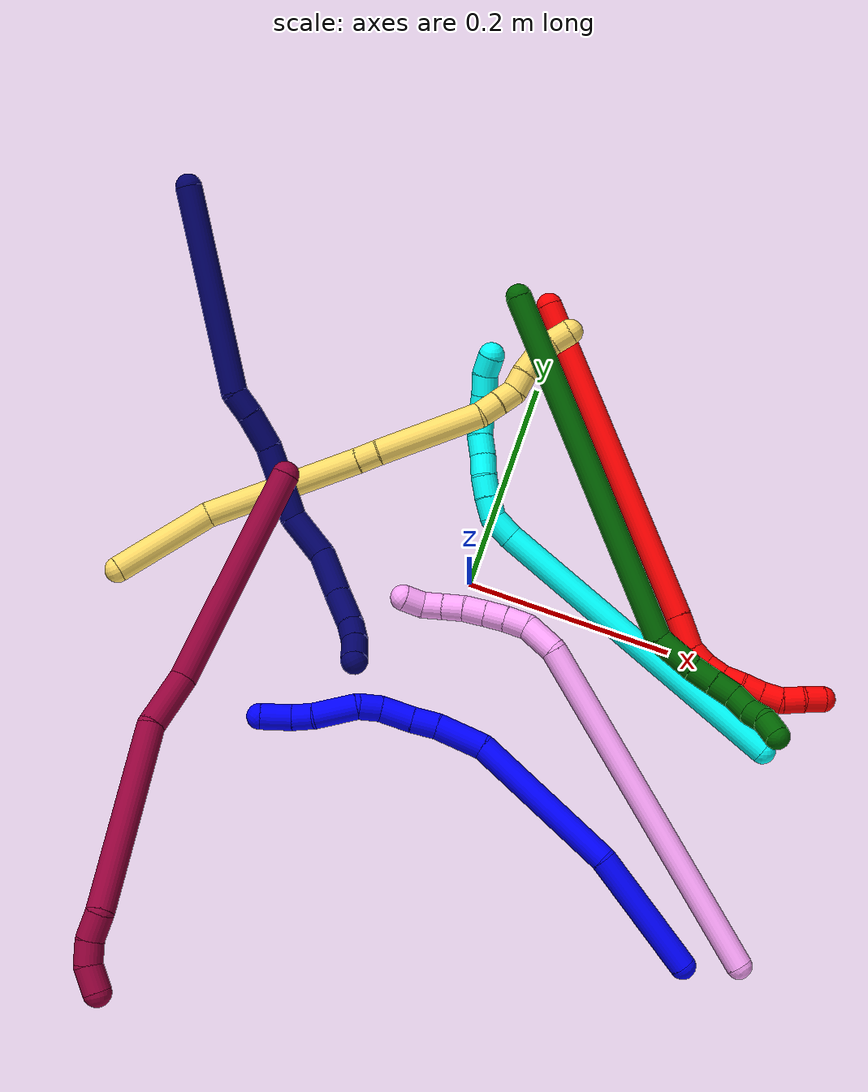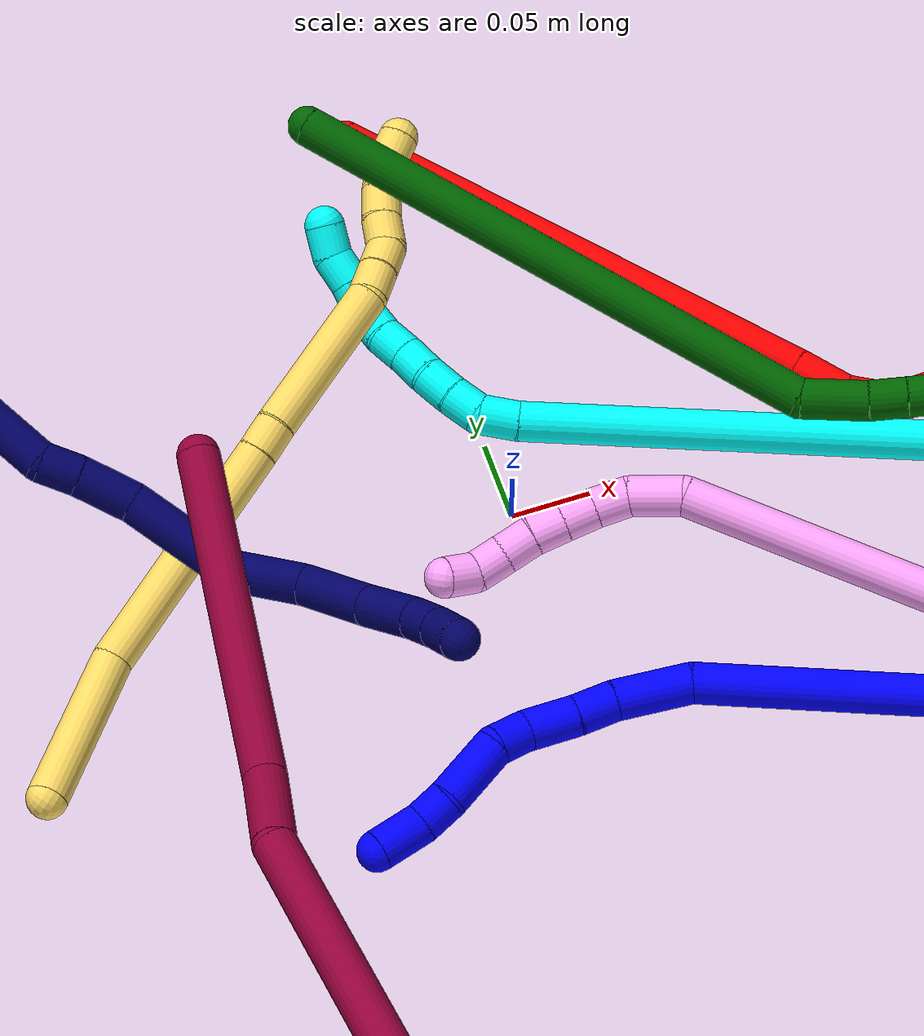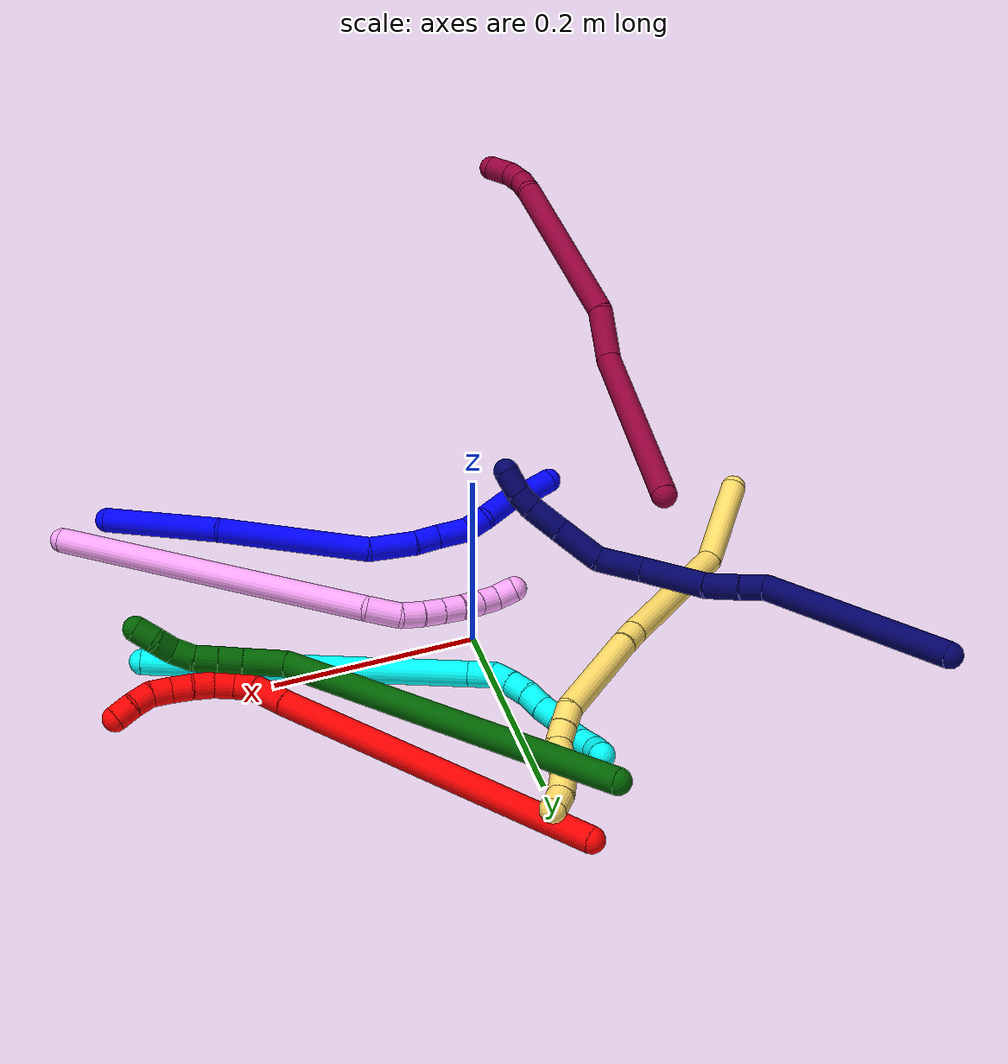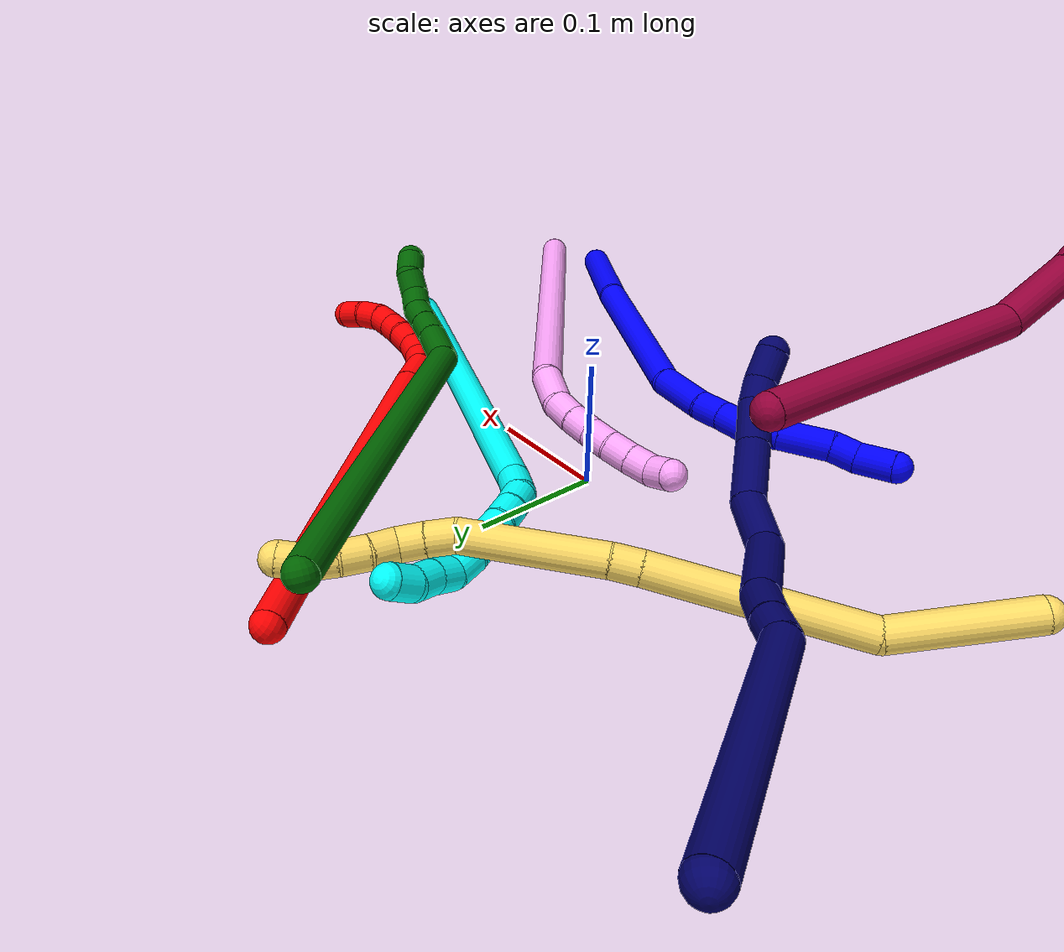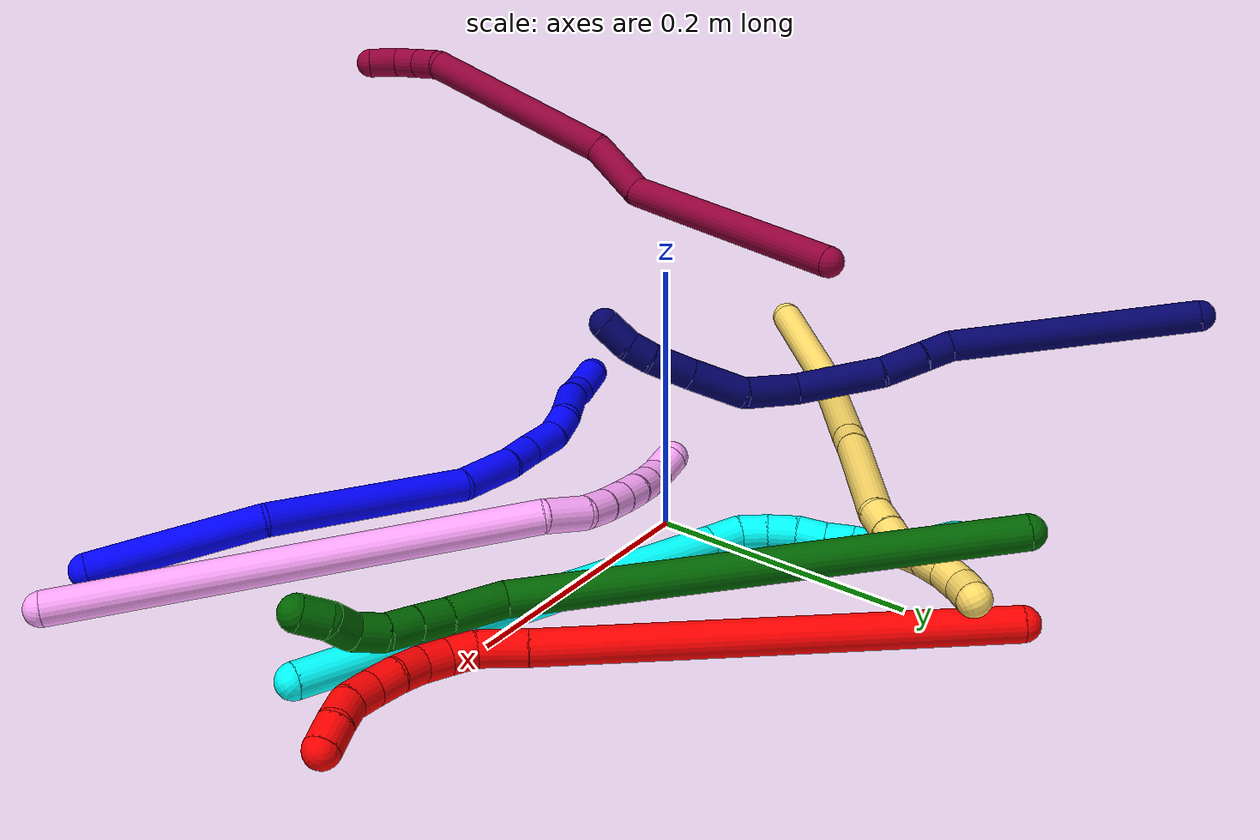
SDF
<sdf version="1.7">
 <world name="default">
  <plugin name="TubeGeneratorPlugin" filename="libtube_generator_plugin.so"/>
  <model name="photoneo_s_sensor">
   <static>1</static>
   <pose>0 0 2 1.57079 1.57079 3.14159</pose>
   <link name="link">
    <inertial><mass>0.1</mass></inertial>
    <sensor name="sensor" type="depth">
     <update_rate>30</update_rate>
     <camera>
      <horizontal_fov>1.22</horizontal_fov>
      <image><width>1920</width><height>1200</height><format>B8G8R8</format></image>
      <clip><near>0.1</near><far>4</far></clip>
      <depth_camera><output>points</output></depth_camera>
     </camera>
     <plugin name="camera_plugin" filename="libgazebo_ros_depth_camera.so">
      <baseline>0.2</baseline>
      <alwaysOn>1</alwaysOn>
      <updateRate>0.0</updateRate>
      <cameraName>camera_ir</cameraName>
      <imageTopicName>/camera/color/image_raw</imageTopicName>
      <cameraInfoTopicName>/camera/color/camera_info</cameraInfoTopicName>
      <depthImageTopicName>/camera/depth/image_raw</depthImageTopicName>
      <depthImageCameraInfoTopicName>/camera/depth/camera_info</depthImageCameraInfoTopicName>
      <pointCloudTopicName>/camera/depth/points</pointCloudTopicName>
      <frameName>fr_optical</frameName>
      <pointCloudCutoff>0.1</pointCloudCutoff>
      <pointCloudCutoffMax>2.0</pointCloudCutoffMax>
      <distortionK1>0</distortionK1>
      <distortionK2>0</distortionK2>
      <distortionK3>0</distortionK3>
      <distortionT1>0</distortionT1>
      <distortionT2>0</distortionT2>
      <CxPrime>0</CxPrime>
      <Cx>0</Cx>
      <Cy>0</Cy>
      <focalLength>0</focalLength>
      <hackBaseline>0</hackBaseline>
     </plugin>
    </sensor>
   </link>
  </model>
  <gravity>0 0 -9.8</gravity>
  <magnetic_field>6e-06 2.3e-05 -4.2e-05</magnetic_field>
  <atmosphere type="adiabatic"/>
  <physics name="default_physics" default="0" type="ode">
   <max_step_size>0.003</max_step_size>
   <real_time_factor>1</real_time_factor>
   <real_time_update_rate>1000</real_time_update_rate>
   <max_contacts>10000</max_contacts>
   <ode>
    <solver>
     <type>quick</type>
     <iters>100</iters>
     <sor>1.3</sor>
     <use_dynamic_moi_rescaling>0</use_dynamic_moi_rescaling>
    </solver>
    <constraints>
     <contact_max_correcting_vel>0</contact_max_correcting_vel>
     <contact_surface_layer>0.001</contact_surface_layer>
     <cfm>0</cfm>
     <erp>0.2</erp>
    </constraints>
   </ode>
  </physics>
  <scene><ambient>0.4 0.4 0.4 1</ambient><background>0.7 0.7 0.7 1</background><shadows>0</shadows></scene>
  <audio><device>default</device></audio>
  <spherical_coordinates>
   <surface_model>EARTH_WGS84</surface_model>
   <latitude_deg>0</latitude_deg>
   <longitude_deg>0</longitude_deg>
   <elevation>0</elevation>
   <heading_deg>0</heading_deg>
  </spherical_coordinates>
  <model name="bin">
   <static>1</static>
   <link name="bottom">
    <collision name="collision-bottom">
     <pose>0 0 -0.01 0 -0 0</pose>
     <geometry><box><size>0.8 0.6 0.02</size></box></geometry>
     <surface>
      <friction><ode><mu>100</mu><mu2>100</mu2></ode></friction>
      <contact><collide_bitmask>65535</collide_bitmask></contact>
     </surface>
    </collision>
   </link>
   <link name="west_wall">
    <collision name="collision-west_wall">
     <pose>-0.41 0 0.1 0 -0 0</pose>
     <geometry><box><size>0.02 0.6 0.2</size></box></geometry>
     <surface>
      <friction><ode><mu>100</mu><mu2>100</mu2></ode></friction>
      <contact><collide_bitmask>65535</collide_bitmask></contact>
     </surface>
    </collision>
   </link>
   <link name="east_wall">
    <collision name="collision-east_wall">
     <pose>0.41 0 0.1 0 -0 0</pose>
     <geometry><box><size>0.02 0.6 0.2</size></box></geometry>
     <surface>
      <friction><ode><mu>100</mu><mu2>100</mu2></ode></friction>
      <contact><collide_bitmask>65535</collide_bitmask></contact>
     </surface>
    </collision>
   </link>
   <link name="south_wall">
    <collision name="collision-south_wall">
     <pose>0 -0.31 0.1 0 -0 0</pose>
     <geometry><box><size>0.8 0.02 0.2</size></box></geometry>
     <surface>
      <friction><ode><mu>100</mu><mu2>100</mu2></ode></friction>
      <contact><collide_bitmask>65535</collide_bitmask></contact>
     </surface>
    </collision>
   </link>
   <link name="north_wall">
    <collision name="collision-north_wall">
     <pose>0 0.31 0.1 0 -0 0</pose>
     <geometry><box><size>0.8 0.02 0.2</size></box></geometry>
     <surface>
      <friction><ode><mu>100</mu><mu2>100</mu2></ode></friction>
      <contact><collide_bitmask>65535</collide_bitmask></contact>
     </surface>
    </collision>
   </link>
  </model>
  <model name="1">
   <static>0</static>
   <link name="1">
    <collision name="collision-cylinder-e_1_1_4">
     <pose>-0.056657 0.025792 0.006387 -1.32805 -1.13228 0.923055</pose>
     <geometry><cylinder><radius>0.0125</radius><length>0.125157</length></cylinder></geometry>
     <surface>
      <friction><ode><mu>1.16</mu><mu2>1.16</mu2><slip1>0</slip1><slip2>0</slip2></ode></friction>
      <contact><ode><kp>1e+06</kp><kd>1</kd><max_vel>0</max_vel><min_depth>0.001</min_depth></ode></contact>
     </surface>
    </collision>
    <visual name="visual-cylinder-e_1_1_4">
     <pose>-0.056657 0.025792 0.006387 -1.32805 -1.13228 0.923055</pose>
     <geometry><cylinder><radius>0.0125</radius><length>0.125157</length></cylinder></geometry>
     <material><ambient>0 0 1 1</ambient></material>
    </visual>
    <collision name="collision-cylinder-e_2_4_5">
     <pose>-0.173585 0.099635 0.01163 -1.5946 -0.897582 0.916332</pose>
     <geometry><cylinder><radius>0.0125</radius><length>0.154178</length></cylinder></geometry>
     <surface>
      <friction><ode><mu>1.16</mu><mu2>1.16</mu2><slip1>0</slip1><slip2>0</slip2></ode></friction>
      <contact><ode><kp>1e+06</kp><kd>1</kd><max_vel>0</max_vel><min_depth>0.001</min_depth></ode></contact>
     </surface>
    </collision>
    <visual name="visual-cylinder-e_2_4_5">
     <pose>-0.173585 0.099635 0.01163 -1.5946 -0.897582 0.916332</pose>
     <geometry><cylinder><radius>0.0125</radius><length>0.154178</length></cylinder></geometry>
     <material><ambient>0 0 1 1</ambient></material>
    </visual>
    <collision name="collision-cylinder-e_3_5_6">
     <pose>-0.250942 0.16202 0.002425 -2.08304 -0.804567 1.25776</pose>
     <geometry><cylinder><radius>0.0125</radius><length>0.047431</length></cylinder></geometry>
     <surface>
      <friction><ode><mu>1.16</mu><mu2>1.16</mu2><slip1>0</slip1><slip2>0</slip2></ode></friction>
      <contact><ode><kp>1e+06</kp><kd>1</kd><max_vel>0</max_vel><min_depth>0.001</min_depth></ode></contact>
     </surface>
    </collision>
    <visual name="visual-cylinder-e_3_5_6">
     <pose>-0.250942 0.16202 0.002425 -2.08304 -0.804567 1.25776</pose>
     <geometry><cylinder><radius>0.0125</radius><length>0.047431</length></cylinder></geometry>
     <material><ambient>0 0 1 1</ambient></material>
    </visual>
    <collision name="collision-cylinder-e_4_6_7">
     <pose>-0.276052 0.1834 -0.011711 -2.28245 -0.711563 1.36301</pose>
     <geometry><cylinder><radius>0.0125</radius><length>0.02457</length></cylinder></geometry>
     <surface>
      <friction><ode><mu>1.16</mu><mu2>1.16</mu2><slip1>0</slip1><slip2>0</slip2></ode></friction>
      <contact><ode><kp>1e+06</kp><kd>1</kd><max_vel>0</max_vel><min_depth>0.001</min_depth></ode></contact>
     </surface>
    </collision>
    <visual name="visual-cylinder-e_4_6_7">
     <pose>-0.276052 0.1834 -0.011711 -2.28245 -0.711563 1.36301</pose>
     <geometry><cylinder><radius>0.0125</radius><length>0.02457</length></cylinder></geometry>
     <material><ambient>0 0 1 1</ambient></material>
    </visual>
    <collision name="collision-cylinder-e_5_7_8">
     <pose>-0.295302 0.199376 -0.024689 -2.22876 -0.782793 1.39792</pose>
     <geometry><cylinder><radius>0.0125</radius><length>0.031841</length></cylinder></geometry>
     <surface>
      <friction><ode><mu>1.16</mu><mu2>1.16</mu2><slip1>0</slip1><slip2>0</slip2></ode></friction>
      <contact><ode><kp>1e+06</kp><kd>1</kd><max_vel>0</max_vel><min_depth>0.001</min_depth></ode></contact>
     </surface>
    </collision>
    <visual name="visual-cylinder-e_5_7_8">
     <pose>-0.295302 0.199376 -0.024689 -2.22876 -0.782793 1.39792</pose>
     <geometry><cylinder><radius>0.0125</radius><length>0.031841</length></cylinder></geometry>
     <material><ambient>0 0 1 1</ambient></material>
    </visual>
    <collision name="collision-cylinder-e_6_8_9">
     <pose>-0.314016 0.212004 -0.03906 -2.68192 -0.731822 2.0452</pose>
     <geometry><cylinder><radius>0.0125</radius><length>0.022403</length></cylinder></geometry>
     <surface>
      <friction><ode><mu>1.16</mu><mu2>1.16</mu2><slip1>0</slip1><slip2>0</slip2></ode></friction>
      <contact><ode><kp>1e+06</kp><kd>1</kd><max_vel>0</max_vel><min_depth>0.001</min_depth></ode></contact>
     </surface>
    </collision>
    <visual name="visual-cylinder-e_6_8_9">
     <pose>-0.314016 0.212004 -0.03906 -2.68192 -0.731822 2.0452</pose>
     <geometry><cylinder><radius>0.0125</radius><length>0.022403</length></cylinder></geometry>
     <material><ambient>0 0 1 1</ambient></material>
    </visual>
    <collision name="collision-cylinder-e_7_9_10">
     <pose>-0.328089 0.226211 -0.063631 -2.59058 -0.31712 1.02954</pose>
     <geometry><cylinder><radius>0.0125</radius><length>0.042254</length></cylinder></geometry>
     <surface>
      <friction><ode><mu>1.16</mu><mu2>1.16</mu2><slip1>0</slip1><slip2>0</slip2></ode></friction>
      <contact><ode><kp>1e+06</kp><kd>1</kd><max_vel>0</max_vel><min_depth>0.001</min_depth></ode></contact>
     </surface>
    </collision>
    <visual name="visual-cylinder-e_7_9_10">
     <pose>-0.328089 0.226211 -0.063631 -2.59058 -0.31712 1.02954</pose>
     <geometry><cylinder><radius>0.0125</radius><length>0.042254</length></cylinder></geometry>
     <material><ambient>0 0 1 1</ambient></material>
    </visual>
    <collision name="collision-cylinder-e_8_10_11">
     <pose>-0.338209 0.243667 -0.087739 -2.36043 -0.343835 0.798159</pose>
     <geometry><cylinder><radius>0.0125</radius><length>0.020959</length></cylinder></geometry>
     <surface>
      <friction><ode><mu>1.16</mu><mu2>1.16</mu2><slip1>0</slip1><slip2>0</slip2></ode></friction>
      <contact><ode><kp>1e+06</kp><kd>1</kd><max_vel>0</max_vel><min_depth>0.001</min_depth></ode></contact>
     </surface>
    </collision>
    <visual name="visual-cylinder-e_8_10_11">
     <pose>-0.338209 0.243667 -0.087739 -2.36043 -0.343835 0.798159</pose>
     <geometry><cylinder><radius>0.0125</radius><length>0.020959</length></cylinder></geometry>
     <material><ambient>0 0 1 1</ambient></material>
    </visual>
    <collision name="collision-cylinder-e_9_11_2">
     <pose>-0.350535 0.257848 -0.105414 -2.54574 -0.598605 1.5757</pose>
     <geometry><cylinder><radius>0.0125</radius><length>0.031208</length></cylinder></geometry>
     <surface>
      <friction><ode><mu>1.16</mu><mu2>1.16</mu2><slip1>0</slip1><slip2>0</slip2></ode></friction>
      <contact><ode><kp>1e+06</kp><kd>1</kd><max_vel>0</max_vel><min_depth>0.001</min_depth></ode></contact>
     </surface>
    </collision>
    <visual name="visual-cylinder-e_9_11_2">
     <pose>-0.350535 0.257848 -0.105414 -2.54574 -0.598605 1.5757</pose>
     <geometry><cylinder><radius>0.0125</radius><length>0.031208</length></cylinder></geometry>
     <material><ambient>0 0 1 1</ambient></material>
    </visual>
    <collision name="collision-sphere-2">
     <pose>-0.359327 0.265082 -0.116084 0 -0 0</pose>
     <geometry><sphere><radius>0.0125</radius></sphere></geometry>
     <surface>
      <friction><ode><mu>1.16</mu><mu2>1.16</mu2><slip1>0</slip1><slip2>0</slip2></ode></friction>
      <contact><ode><kp>1e+06</kp><kd>1</kd><max_vel>0</max_vel><min_depth>0.001</min_depth></ode></contact>
     </surface>
    </collision>
    <visual name="visual-sphere-2">
     <pose>-0.359327 0.265082 -0.116084 0 -0 0</pose>
     <geometry><sphere><radius>0.0125</radius></sphere></geometry>
     <material><ambient>0 0 1 1</ambient></material>
    </visual>
    <collision name="collision-sphere-11">
     <pose>-0.341742 0.250613 -0.094745 0 -0 0</pose>
     <geometry><sphere><radius>0.0125</radius></sphere></geometry>
     <surface>
      <friction><ode><mu>1.16</mu><mu2>1.16</mu2><slip1>0</slip1><slip2>0</slip2></ode></friction>
      <contact><ode><kp>1e+06</kp><kd>1</kd><max_vel>0</max_vel><min_depth>0.001</min_depth></ode></contact>
     </surface>
    </collision>
    <visual name="visual-sphere-11">
     <pose>-0.341742 0.250613 -0.094745 0 -0 0</pose>
     <geometry><sphere><radius>0.0125</radius></sphere></geometry>
     <material><ambient>0 0 1 1</ambient></material>
    </visual>
    <collision name="collision-sphere-10">
     <pose>-0.334677 0.23672 -0.080733 0 -0 0</pose>
     <geometry><sphere><radius>0.0125</radius></sphere></geometry>
     <surface>
      <friction><ode><mu>1.16</mu><mu2>1.16</mu2><slip1>0</slip1><slip2>0</slip2></ode></friction>
      <contact><ode><kp>1e+06</kp><kd>1</kd><max_vel>0</max_vel><min_depth>0.001</min_depth></ode></contact>
     </surface>
    </collision>
    <visual name="visual-sphere-10">
     <pose>-0.334677 0.23672 -0.080733 0 -0 0</pose>
     <geometry><sphere><radius>0.0125</radius></sphere></geometry>
     <material><ambient>0 0 1 1</ambient></material>
    </visual>
    <collision name="collision-sphere-9">
     <pose>-0.321501 0.215701 -0.046528 0 -0 0</pose>
     <geometry><sphere><radius>0.0125</radius></sphere></geometry>
     <surface>
      <friction><ode><mu>1.16</mu><mu2>1.16</mu2><slip1>0</slip1><slip2>0</slip2></ode></friction>
      <contact><ode><kp>1e+06</kp><kd>1</kd><max_vel>0</max_vel><min_depth>0.001</min_depth></ode></contact>
     </surface>
    </collision>
    <visual name="visual-sphere-9">
     <pose>-0.321501 0.215701 -0.046528 0 -0 0</pose>
     <geometry><sphere><radius>0.0125</radius></sphere></geometry>
     <material><ambient>0 0 1 1</ambient></material>
    </visual>
    <collision name="collision-sphere-4">
     <pose>-0.113315 0.051583 0.012774 0 -0 0</pose>
     <geometry><sphere><radius>0.0125</radius></sphere></geometry>
     <surface>
      <friction><ode><mu>1.16</mu><mu2>1.16</mu2><slip1>0</slip1><slip2>0</slip2></ode></friction>
      <contact><ode><kp>1e+06</kp><kd>1</kd><max_vel>0</max_vel><min_depth>0.001</min_depth></ode></contact>
     </surface>
    </collision>
    <visual name="visual-sphere-4">
     <pose>-0.113315 0.051583 0.012774 0 -0 0</pose>
     <geometry><sphere><radius>0.0125</radius></sphere></geometry>
     <material><ambient>0 0 1 1</ambient></material>
    </visual>
    <collision name="collision-sphere-1">
     <geometry><sphere><radius>0.0125</radius></sphere></geometry>
     <surface>
      <friction><ode><mu>1.16</mu><mu2>1.16</mu2><slip1>0</slip1><slip2>0</slip2></ode></friction>
      <contact><ode><kp>1e+06</kp><kd>1</kd><max_vel>0</max_vel><min_depth>0.001</min_depth></ode></contact>
     </surface>
    </collision>
    <visual name="visual-sphere-1">
     <geometry><sphere><radius>0.0125</radius></sphere></geometry>
     <material><ambient>0 0 1 1</ambient></material>
    </visual>
    <collision name="collision-sphere-8">
     <pose>-0.30653 0.208307 -0.031591 0 -0 0</pose>
     <geometry><sphere><radius>0.0125</radius></sphere></geometry>
     <surface>
      <friction><ode><mu>1.16</mu><mu2>1.16</mu2><slip1>0</slip1><slip2>0</slip2></ode></friction>
      <contact><ode><kp>1e+06</kp><kd>1</kd><max_vel>0</max_vel><min_depth>0.001</min_depth></ode></contact>
     </surface>
    </collision>
    <visual name="visual-sphere-8">
     <pose>-0.30653 0.208307 -0.031591 0 -0 0</pose>
     <geometry><sphere><radius>0.0125</radius></sphere></geometry>
     <material><ambient>0 0 1 1</ambient></material>
    </visual>
    <collision name="collision-sphere-5">
     <pose>-0.233854 0.147686 0.010486 0 -0 0</pose>
     <geometry><sphere><radius>0.0125</radius></sphere></geometry>
     <surface>
      <friction><ode><mu>1.16</mu><mu2>1.16</mu2><slip1>0</slip1><slip2>0</slip2></ode></friction>
      <contact><ode><kp>1e+06</kp><kd>1</kd><max_vel>0</max_vel><min_depth>0.001</min_depth></ode></contact>
     </surface>
    </collision>
    <visual name="visual-sphere-5">
     <pose>-0.233854 0.147686 0.010486 0 -0 0</pose>
     <geometry><sphere><radius>0.0125</radius></sphere></geometry>
     <material><ambient>0 0 1 1</ambient></material>
    </visual>
    <collision name="collision-sphere-6">
     <pose>-0.268029 0.176354 -0.005635 0 -0 0</pose>
     <geometry><sphere><radius>0.0125</radius></sphere></geometry>
     <surface>
      <friction><ode><mu>1.16</mu><mu2>1.16</mu2><slip1>0</slip1><slip2>0</slip2></ode></friction>
      <contact><ode><kp>1e+06</kp><kd>1</kd><max_vel>0</max_vel><min_depth>0.001</min_depth></ode></contact>
     </surface>
    </collision>
    <visual name="visual-sphere-6">
     <pose>-0.268029 0.176354 -0.005635 0 -0 0</pose>
     <geometry><sphere><radius>0.0125</radius></sphere></geometry>
     <material><ambient>0 0 1 1</ambient></material>
    </visual>
    <collision name="collision-sphere-7">
     <pose>-0.284074 0.190446 -0.017787 0 -0 0</pose>
     <geometry><sphere><radius>0.0125</radius></sphere></geometry>
     <surface>
      <friction><ode><mu>1.16</mu><mu2>1.16</mu2><slip1>0</slip1><slip2>0</slip2></ode></friction>
      <contact><ode><kp>1e+06</kp><kd>1</kd><max_vel>0</max_vel><min_depth>0.001</min_depth></ode></contact>
     </surface>
    </collision>
    <visual name="visual-sphere-7">
     <pose>-0.284074 0.190446 -0.017787 0 -0 0</pose>
     <geometry><sphere><radius>0.0125</radius></sphere></geometry>
     <material><ambient>0 0 1 1</ambient></material>
    </visual>
    <inertial>
     <pose>-0.201735 0.129181 -0.014118 0 -0 0</pose>
     <mass>0.5</mass>
     <inertia>
      <ixx>0.000375</ixx>
      <ixy>0</ixy>
      <ixz>0</ixz>
      <iyy>0.000593</iyy>
      <iyz>0</iyz>
      <izz>0.000124</izz>
     </inertia>
    </inertial>
   </link>
   <pose>0.306518 -0.275424 0.0115 -1.85478 0.561864 -0.61046</pose>
  </model>
  <model name="2">
   <static>0</static>
   <link name="2">
    <collision name="collision-cylinder-e_1_1_4">
     <pose>0.088199 -0.131737 -0.037337 1.84697 0.572246 0.74226</pose>
     <geometry><cylinder><radius>0.0125</radius><length>0.325747</length></cylinder></geometry>
     <surface>
      <friction><ode><mu>1.16</mu><mu2>1.16</mu2><slip1>0</slip1><slip2>0</slip2></ode></friction>
      <contact><ode><kp>1e+06</kp><kd>1</kd><max_vel>0</max_vel><min_depth>0.001</min_depth></ode></contact>
     </surface>
    </collision>
    <visual name="visual-cylinder-e_1_1_4">
     <pose>0.088199 -0.131737 -0.037337 1.84697 0.572246 0.74226</pose>
     <geometry><cylinder><radius>0.0125</radius><length>0.325747</length></cylinder></geometry>
     <material><ambient>1 0 0 1</ambient></material>
    </visual>
    <collision name="collision-cylinder-e_2_4_5">
     <pose>0.185001 -0.277449 -0.079038 1.87346 0.531196 0.708617</pose>
     <geometry><cylinder><radius>0.0125</radius><length>0.033962</length></cylinder></geometry>
     <surface>
      <friction><ode><mu>1.16</mu><mu2>1.16</mu2><slip1>0</slip1><slip2>0</slip2></ode></friction>
      <contact><ode><kp>1e+06</kp><kd>1</kd><max_vel>0</max_vel><min_depth>0.001</min_depth></ode></contact>
     </surface>
    </collision>
    <visual name="visual-cylinder-e_2_4_5">
     <pose>0.185001 -0.277449 -0.079038 1.87346 0.531196 0.708617</pose>
     <geometry><cylinder><radius>0.0125</radius><length>0.033962</length></cylinder></geometry>
     <material><ambient>1 0 0 1</ambient></material>
    </visual>
    <collision name="collision-cylinder-e_3_5_6">
     <pose>0.201107 -0.298041 -0.083294 1.55454 0.848144 0.836018</pose>
     <geometry><cylinder><radius>0.0125</radius><length>0.020009</length></cylinder></geometry>
     <surface>
      <friction><ode><mu>1.16</mu><mu2>1.16</mu2><slip1>0</slip1><slip2>0</slip2></ode></friction>
      <contact><ode><kp>1e+06</kp><kd>1</kd><max_vel>0</max_vel><min_depth>0.001</min_depth></ode></contact>
     </surface>
    </collision>
    <visual name="visual-cylinder-e_3_5_6">
     <pose>0.201107 -0.298041 -0.083294 1.55454 0.848144 0.836018</pose>
     <geometry><cylinder><radius>0.0125</radius><length>0.020009</length></cylinder></geometry>
     <material><ambient>1 0 0 1</ambient></material>
    </visual>
    <collision name="collision-cylinder-e_4_6_7">
     <pose>0.216197 -0.310794 -0.080692 1.18477 0.852912 0.593498</pose>
     <geometry><cylinder><radius>0.0125</radius><length>0.020143</length></cylinder></geometry>
     <surface>
      <friction><ode><mu>1.16</mu><mu2>1.16</mu2><slip1>0</slip1><slip2>0</slip2></ode></friction>
      <contact><ode><kp>1e+06</kp><kd>1</kd><max_vel>0</max_vel><min_depth>0.001</min_depth></ode></contact>
     </surface>
    </collision>
    <visual name="visual-cylinder-e_4_6_7">
     <pose>0.216197 -0.310794 -0.080692 1.18477 0.852912 0.593498</pose>
     <geometry><cylinder><radius>0.0125</radius><length>0.020143</length></cylinder></geometry>
     <material><ambient>1 0 0 1</ambient></material>
    </visual>
    <collision name="collision-cylinder-e_5_7_8">
     <pose>0.231517 -0.321587 -0.073797 0.813567 0.879055 0.39973</pose>
     <geometry><cylinder><radius>0.0125</radius><length>0.020086</length></cylinder></geometry>
     <surface>
      <friction><ode><mu>1.16</mu><mu2>1.16</mu2><slip1>0</slip1><slip2>0</slip2></ode></friction>
      <contact><ode><kp>1e+06</kp><kd>1</kd><max_vel>0</max_vel><min_depth>0.001</min_depth></ode></contact>
     </surface>
    </collision>
    <visual name="visual-cylinder-e_5_7_8">
     <pose>0.231517 -0.321587 -0.073797 0.813567 0.879055 0.39973</pose>
     <geometry><cylinder><radius>0.0125</radius><length>0.020086</length></cylinder></geometry>
     <material><ambient>1 0 0 1</ambient></material>
    </visual>
    <collision name="collision-cylinder-e_6_8_9">
     <pose>0.247744 -0.330522 -0.066244 0.93589 1.01159 0.545844</pose>
     <geometry><cylinder><radius>0.0125</radius><length>0.020036</length></cylinder></geometry>
     <surface>
      <friction><ode><mu>1.16</mu><mu2>1.16</mu2><slip1>0</slip1><slip2>0</slip2></ode></friction>
      <contact><ode><kp>1e+06</kp><kd>1</kd><max_vel>0</max_vel><min_depth>0.001</min_depth></ode></contact>
     </surface>
    </collision>
    <visual name="visual-cylinder-e_6_8_9">
     <pose>0.247744 -0.330522 -0.066244 0.93589 1.01159 0.545844</pose>
     <geometry><cylinder><radius>0.0125</radius><length>0.020036</length></cylinder></geometry>
     <material><ambient>1 0 0 1</ambient></material>
    </visual>
    <collision name="collision-cylinder-e_7_9_10">
     <pose>0.264366 -0.338481 -0.058563 0.682361 0.948275 0.360472</pose>
     <geometry><cylinder><radius>0.0125</radius><length>0.020017</length></cylinder></geometry>
     <surface>
      <friction><ode><mu>1.16</mu><mu2>1.16</mu2><slip1>0</slip1><slip2>0</slip2></ode></friction>
      <contact><ode><kp>1e+06</kp><kd>1</kd><max_vel>0</max_vel><min_depth>0.001</min_depth></ode></contact>
     </surface>
    </collision>
    <visual name="visual-cylinder-e_7_9_10">
     <pose>0.264366 -0.338481 -0.058563 0.682361 0.948275 0.360472</pose>
     <geometry><cylinder><radius>0.0125</radius><length>0.020017</length></cylinder></geometry>
     <material><ambient>1 0 0 1</ambient></material>
    </visual>
    <collision name="collision-cylinder-e_8_10_11">
     <pose>0.280776 -0.342061 -0.048426 -0.017856 0.975349 -0.009471</pose>
     <geometry><cylinder><radius>0.0125</radius><length>0.02</length></cylinder></geometry>
     <surface>
      <friction><ode><mu>1.16</mu><mu2>1.16</mu2><slip1>0</slip1><slip2>0</slip2></ode></friction>
      <contact><ode><kp>1e+06</kp><kd>1</kd><max_vel>0</max_vel><min_depth>0.001</min_depth></ode></contact>
     </surface>
    </collision>
    <visual name="visual-cylinder-e_8_10_11">
     <pose>0.280776 -0.342061 -0.048426 -0.017856 0.975349 -0.009471</pose>
     <geometry><cylinder><radius>0.0125</radius><length>0.02</length></cylinder></geometry>
     <material><ambient>1 0 0 1</ambient></material>
    </visual>
    <collision name="collision-cylinder-e_9_11_2">
     <pose>0.298215 -0.341112 -0.038897 -0.213189 1.15789 -0.139656</pose>
     <geometry><cylinder><radius>0.0125</radius><length>0.02</length></cylinder></geometry>
     <surface>
      <friction><ode><mu>1.16</mu><mu2>1.16</mu2><slip1>0</slip1><slip2>0</slip2></ode></friction>
      <contact><ode><kp>1e+06</kp><kd>1</kd><max_vel>0</max_vel><min_depth>0.001</min_depth></ode></contact>
     </surface>
    </collision>
    <visual name="visual-cylinder-e_9_11_2">
     <pose>0.298215 -0.341112 -0.038897 -0.213189 1.15789 -0.139656</pose>
     <geometry><cylinder><radius>0.0125</radius><length>0.02</length></cylinder></geometry>
     <material><ambient>1 0 0 1</ambient></material>
    </visual>
    <collision name="collision-sphere-2">
     <pose>0.307375 -0.340263 -0.034975 0 -0 0</pose>
     <geometry><sphere><radius>0.0125</radius></sphere></geometry>
     <surface>
      <friction><ode><mu>1.16</mu><mu2>1.16</mu2><slip1>0</slip1><slip2>0</slip2></ode></friction>
      <contact><ode><kp>1e+06</kp><kd>1</kd><max_vel>0</max_vel><min_depth>0.001</min_depth></ode></contact>
     </surface>
    </collision>
    <visual name="visual-sphere-2">
     <pose>0.307375 -0.340263 -0.034975 0 -0 0</pose>
     <geometry><sphere><radius>0.0125</radius></sphere></geometry>
     <material><ambient>1 0 0 1</ambient></material>
    </visual>
    <collision name="collision-sphere-11">
     <pose>0.289055 -0.341961 -0.042818 0 -0 0</pose>
     <geometry><sphere><radius>0.0125</radius></sphere></geometry>
     <surface>
      <friction><ode><mu>1.16</mu><mu2>1.16</mu2><slip1>0</slip1><slip2>0</slip2></ode></friction>
      <contact><ode><kp>1e+06</kp><kd>1</kd><max_vel>0</max_vel><min_depth>0.001</min_depth></ode></contact>
     </surface>
    </collision>
    <visual name="visual-sphere-11">
     <pose>0.289055 -0.341961 -0.042818 0 -0 0</pose>
     <geometry><sphere><radius>0.0125</radius></sphere></geometry>
     <material><ambient>1 0 0 1</ambient></material>
    </visual>
    <collision name="collision-sphere-10">
     <pose>0.272497 -0.342161 -0.054034 0 -0 0</pose>
     <geometry><sphere><radius>0.0125</radius></sphere></geometry>
     <surface>
      <friction><ode><mu>1.16</mu><mu2>1.16</mu2><slip1>0</slip1><slip2>0</slip2></ode></friction>
      <contact><ode><kp>1e+06</kp><kd>1</kd><max_vel>0</max_vel><min_depth>0.001</min_depth></ode></contact>
     </surface>
    </collision>
    <visual name="visual-sphere-10">
     <pose>0.272497 -0.342161 -0.054034 0 -0 0</pose>
     <geometry><sphere><radius>0.0125</radius></sphere></geometry>
     <material><ambient>1 0 0 1</ambient></material>
    </visual>
    <collision name="collision-sphere-9">
     <pose>0.256235 -0.334801 -0.063092 0 -0 0</pose>
     <geometry><sphere><radius>0.0125</radius></sphere></geometry>
     <surface>
      <friction><ode><mu>1.16</mu><mu2>1.16</mu2><slip1>0</slip1><slip2>0</slip2></ode></friction>
      <contact><ode><kp>1e+06</kp><kd>1</kd><max_vel>0</max_vel><min_depth>0.001</min_depth></ode></contact>
     </surface>
    </collision>
    <visual name="visual-sphere-9">
     <pose>0.256235 -0.334801 -0.063092 0 -0 0</pose>
     <geometry><sphere><radius>0.0125</radius></sphere></geometry>
     <material><ambient>1 0 0 1</ambient></material>
    </visual>
    <collision name="collision-sphere-4">
     <pose>0.176399 -0.263473 -0.074674 0 -0 0</pose>
     <geometry><sphere><radius>0.0125</radius></sphere></geometry>
     <surface>
      <friction><ode><mu>1.16</mu><mu2>1.16</mu2><slip1>0</slip1><slip2>0</slip2></ode></friction>
      <contact><ode><kp>1e+06</kp><kd>1</kd><max_vel>0</max_vel><min_depth>0.001</min_depth></ode></contact>
     </surface>
    </collision>
    <visual name="visual-sphere-4">
     <pose>0.176399 -0.263473 -0.074674 0 -0 0</pose>
     <geometry><sphere><radius>0.0125</radius></sphere></geometry>
     <material><ambient>1 0 0 1</ambient></material>
    </visual>
    <collision name="collision-sphere-1">
     <geometry><sphere><radius>0.0125</radius></sphere></geometry>
     <surface>
      <friction><ode><mu>1.16</mu><mu2>1.16</mu2><slip1>0</slip1><slip2>0</slip2></ode></friction>
      <contact><ode><kp>1e+06</kp><kd>1</kd><max_vel>0</max_vel><min_depth>0.001</min_depth></ode></contact>
     </surface>
    </collision>
    <visual name="visual-sphere-1">
     <geometry><sphere><radius>0.0125</radius></sphere></geometry>
     <material><ambient>1 0 0 1</ambient></material>
    </visual>
    <collision name="collision-sphere-8">
     <pose>0.239252 -0.326243 -0.069397 0 -0 0</pose>
     <geometry><sphere><radius>0.0125</radius></sphere></geometry>
     <surface>
      <friction><ode><mu>1.16</mu><mu2>1.16</mu2><slip1>0</slip1><slip2>0</slip2></ode></friction>
      <contact><ode><kp>1e+06</kp><kd>1</kd><max_vel>0</max_vel><min_depth>0.001</min_depth></ode></contact>
     </surface>
    </collision>
    <visual name="visual-sphere-8">
     <pose>0.239252 -0.326243 -0.069397 0 -0 0</pose>
     <geometry><sphere><radius>0.0125</radius></sphere></geometry>
     <material><ambient>1 0 0 1</ambient></material>
    </visual>
    <collision name="collision-sphere-5">
     <pose>0.193603 -0.291425 -0.083401 0 -0 0</pose>
     <geometry><sphere><radius>0.0125</radius></sphere></geometry>
     <surface>
      <friction><ode><mu>1.16</mu><mu2>1.16</mu2><slip1>0</slip1><slip2>0</slip2></ode></friction>
      <contact><ode><kp>1e+06</kp><kd>1</kd><max_vel>0</max_vel><min_depth>0.001</min_depth></ode></contact>
     </surface>
    </collision>
    <visual name="visual-sphere-5">
     <pose>0.193603 -0.291425 -0.083401 0 -0 0</pose>
     <geometry><sphere><radius>0.0125</radius></sphere></geometry>
     <material><ambient>1 0 0 1</ambient></material>
    </visual>
    <collision name="collision-sphere-6">
     <pose>0.208611 -0.304656 -0.083186 0 -0 0</pose>
     <geometry><sphere><radius>0.0125</radius></sphere></geometry>
     <surface>
      <friction><ode><mu>1.16</mu><mu2>1.16</mu2><slip1>0</slip1><slip2>0</slip2></ode></friction>
      <contact><ode><kp>1e+06</kp><kd>1</kd><max_vel>0</max_vel><min_depth>0.001</min_depth></ode></contact>
     </surface>
    </collision>
    <visual name="visual-sphere-6">
     <pose>0.208611 -0.304656 -0.083186 0 -0 0</pose>
     <geometry><sphere><radius>0.0125</radius></sphere></geometry>
     <material><ambient>1 0 0 1</ambient></material>
    </visual>
    <collision name="collision-sphere-7">
     <pose>0.223783 -0.316932 -0.078198 0 -0 0</pose>
     <geometry><sphere><radius>0.0125</radius></sphere></geometry>
     <surface>
      <friction><ode><mu>1.16</mu><mu2>1.16</mu2><slip1>0</slip1><slip2>0</slip2></ode></friction>
      <contact><ode><kp>1e+06</kp><kd>1</kd><max_vel>0</max_vel><min_depth>0.001</min_depth></ode></contact>
     </surface>
    </collision>
    <visual name="visual-sphere-7">
     <pose>0.223783 -0.316932 -0.078198 0 -0 0</pose>
     <geometry><sphere><radius>0.0125</radius></sphere></geometry>
     <material><ambient>1 0 0 1</ambient></material>
    </visual>
    <inertial>
     <pose>0.139756 -0.19616 -0.047734 0 -0 0</pose>
     <mass>0.5</mass>
     <inertia>
      <ixx>0.003473</ixx>
      <ixy>0</ixy>
      <ixz>0</ixz>
      <iyy>0.002069</iyy>
      <iyz>0</iyz>
      <izz>0.000767</izz>
     </inertia>
    </inertial>
   </link>
   <pose>-0.015959 0.28051 0.011531 -0.674561 0.541079 0.032598</pose>
  </model>
  <model name="3">
   <static>0</static>
   <link name="3">
    <collision name="collision-cylinder-e_1_1_4">
     <pose>-0.130202 0.056886 0.065274 -0.716845 -0.983953 0.396254</pose>
     <geometry><cylinder><radius>0.0125</radius><length>0.312724</length></cylinder></geometry>
     <surface>
      <friction><ode><mu>1.16</mu><mu2>1.16</mu2><slip1>0</slip1><slip2>0</slip2></ode></friction>
      <contact><ode><kp>1e+06</kp><kd>1</kd><max_vel>0</max_vel><min_depth>0.001</min_depth></ode></contact>
     </surface>
    </collision>
    <visual name="visual-cylinder-e_1_1_4">
     <pose>-0.130202 0.056886 0.065274 -0.716845 -0.983953 0.396254</pose>
     <geometry><cylinder><radius>0.0125</radius><length>0.312724</length></cylinder></geometry>
     <material><ambient>0.003922 1 0.996078 1</ambient></material>
    </visual>
    <collision name="collision-cylinder-e_2_4_5">
     <pose>-0.269937 0.118019 0.137165 -0.570523 -0.881081 0.274767</pose>
     <geometry><cylinder><radius>0.0125</radius><length>0.024717</length></cylinder></geometry>
     <surface>
      <friction><ode><mu>1.16</mu><mu2>1.16</mu2><slip1>0</slip1><slip2>0</slip2></ode></friction>
      <contact><ode><kp>1e+06</kp><kd>1</kd><max_vel>0</max_vel><min_depth>0.001</min_depth></ode></contact>
     </surface>
    </collision>
    <visual name="visual-cylinder-e_2_4_5">
     <pose>-0.269937 0.118019 0.137165 -0.570523 -0.881081 0.274767</pose>
     <geometry><cylinder><radius>0.0125</radius><length>0.024717</length></cylinder></geometry>
     <material><ambient>0.003922 1 0.996078 1</ambient></material>
    </visual>
    <collision name="collision-cylinder-e_3_5_6">
     <pose>-0.283347 0.128082 0.151321 -0.657228 -0.386729 0.133336</pose>
     <geometry><cylinder><radius>0.0125</radius><length>0.020559</length></cylinder></geometry>
     <surface>
      <friction><ode><mu>1.16</mu><mu2>1.16</mu2><slip1>0</slip1><slip2>0</slip2></ode></friction>
      <contact><ode><kp>1e+06</kp><kd>1</kd><max_vel>0</max_vel><min_depth>0.001</min_depth></ode></contact>
     </surface>
    </collision>
    <visual name="visual-cylinder-e_3_5_6">
     <pose>-0.283347 0.128082 0.151321 -0.657228 -0.386729 0.133336</pose>
     <geometry><cylinder><radius>0.0125</radius><length>0.020559</length></cylinder></geometry>
     <material><ambient>0.003922 1 0.996078 1</ambient></material>
    </visual>
    <collision name="collision-cylinder-e_4_6_7">
     <pose>-0.290229 0.140226 0.166461 -0.694114 -0.294932 0.107353</pose>
     <geometry><cylinder><radius>0.0125</radius><length>0.020677</length></cylinder></geometry>
     <surface>
      <friction><ode><mu>1.16</mu><mu2>1.16</mu2><slip1>0</slip1><slip2>0</slip2></ode></friction>
      <contact><ode><kp>1e+06</kp><kd>1</kd><max_vel>0</max_vel><min_depth>0.001</min_depth></ode></contact>
     </surface>
    </collision>
    <visual name="visual-cylinder-e_4_6_7">
     <pose>-0.290229 0.140226 0.166461 -0.694114 -0.294932 0.107353</pose>
     <geometry><cylinder><radius>0.0125</radius><length>0.020677</length></cylinder></geometry>
     <material><ambient>0.003922 1 0.996078 1</ambient></material>
    </visual>
    <collision name="collision-cylinder-e_5_7_8">
     <pose>-0.294928 0.154043 0.180759 -0.841339 -0.167064 0.07488</pose>
     <geometry><cylinder><radius>0.0125</radius><length>0.020373</length></cylinder></geometry>
     <surface>
      <friction><ode><mu>1.16</mu><mu2>1.16</mu2><slip1>0</slip1><slip2>0</slip2></ode></friction>
      <contact><ode><kp>1e+06</kp><kd>1</kd><max_vel>0</max_vel><min_depth>0.001</min_depth></ode></contact>
     </surface>
    </collision>
    <visual name="visual-cylinder-e_5_7_8">
     <pose>-0.294928 0.154043 0.180759 -0.841339 -0.167064 0.07488</pose>
     <geometry><cylinder><radius>0.0125</radius><length>0.020373</length></cylinder></geometry>
     <material><ambient>0.003922 1 0.996078 1</ambient></material>
    </visual>
    <collision name="collision-cylinder-e_6_8_9">
     <pose>-0.299207 0.168179 0.194467 -0.758597 -0.261395 0.104694</pose>
     <geometry><cylinder><radius>0.0125</radius><length>0.020006</length></cylinder></geometry>
     <surface>
      <friction><ode><mu>1.16</mu><mu2>1.16</mu2><slip1>0</slip1><slip2>0</slip2></ode></friction>
      <contact><ode><kp>1e+06</kp><kd>1</kd><max_vel>0</max_vel><min_depth>0.001</min_depth></ode></contact>
     </surface>
    </collision>
    <visual name="visual-cylinder-e_6_8_9">
     <pose>-0.299207 0.168179 0.194467 -0.758597 -0.261395 0.104694</pose>
     <geometry><cylinder><radius>0.0125</radius><length>0.020006</length></cylinder></geometry>
     <material><ambient>0.003922 1 0.996078 1</ambient></material>
    </visual>
    <collision name="collision-cylinder-e_7_9_10">
     <pose>-0.302418 0.182111 0.208759 -0.785794 -0.060696 0.025162</pose>
     <geometry><cylinder><radius>0.0125</radius><length>0.020633</length></cylinder></geometry>
     <surface>
      <friction><ode><mu>1.16</mu><mu2>1.16</mu2><slip1>0</slip1><slip2>0</slip2></ode></friction>
      <contact><ode><kp>1e+06</kp><kd>1</kd><max_vel>0</max_vel><min_depth>0.001</min_depth></ode></contact>
     </surface>
    </collision>
    <visual name="visual-cylinder-e_7_9_10">
     <pose>-0.302418 0.182111 0.208759 -0.785794 -0.060696 0.025162</pose>
     <geometry><cylinder><radius>0.0125</radius><length>0.020633</length></cylinder></geometry>
     <material><ambient>0.003922 1 0.996078 1</ambient></material>
    </visual>
    <collision name="collision-cylinder-e_8_10_11">
     <pose>-0.302711 0.1927 0.225587 -0.333167 0.032924 -0.005536</pose>
     <geometry><cylinder><radius>0.0125</radius><length>0.020221</length></cylinder></geometry>
     <surface>
      <friction><ode><mu>1.16</mu><mu2>1.16</mu2><slip1>0</slip1><slip2>0</slip2></ode></friction>
      <contact><ode><kp>1e+06</kp><kd>1</kd><max_vel>0</max_vel><min_depth>0.001</min_depth></ode></contact>
     </surface>
    </collision>
    <visual name="visual-cylinder-e_8_10_11">
     <pose>-0.302711 0.1927 0.225587 -0.333167 0.032924 -0.005536</pose>
     <geometry><cylinder><radius>0.0125</radius><length>0.020221</length></cylinder></geometry>
     <material><ambient>0.003922 1 0.996078 1</ambient></material>
    </visual>
    <collision name="collision-cylinder-e_9_11_12">
     <pose>-0.303257 0.199831 0.24437 -0.392885 -0.087689 0.017462</pose>
     <geometry><cylinder><radius>0.0125</radius><length>0.020067</length></cylinder></geometry>
     <surface>
      <friction><ode><mu>1.16</mu><mu2>1.16</mu2><slip1>0</slip1><slip2>0</slip2></ode></friction>
      <contact><ode><kp>1e+06</kp><kd>1</kd><max_vel>0</max_vel><min_depth>0.001</min_depth></ode></contact>
     </surface>
    </collision>
    <visual name="visual-cylinder-e_9_11_12">
     <pose>-0.303257 0.199831 0.24437 -0.392885 -0.087689 0.017462</pose>
     <geometry><cylinder><radius>0.0125</radius><length>0.020067</length></cylinder></geometry>
     <material><ambient>0.003922 1 0.996078 1</ambient></material>
    </visual>
    <collision name="collision-cylinder-e_10_12_2">
     <pose>-0.302075 0.205246 0.263271 -0.162795 0.207368 -0.016977</pose>
     <geometry><cylinder><radius>0.0125</radius><length>0.020023</length></cylinder></geometry>
     <surface>
      <friction><ode><mu>1.16</mu><mu2>1.16</mu2><slip1>0</slip1><slip2>0</slip2></ode></friction>
      <contact><ode><kp>1e+06</kp><kd>1</kd><max_vel>0</max_vel><min_depth>0.001</min_depth></ode></contact>
     </surface>
    </collision>
    <visual name="visual-cylinder-e_10_12_2">
     <pose>-0.302075 0.205246 0.263271 -0.162795 0.207368 -0.016977</pose>
     <geometry><cylinder><radius>0.0125</radius><length>0.020023</length></cylinder></geometry>
     <material><ambient>0.003922 1 0.996078 1</ambient></material>
    </visual>
    <collision name="collision-sphere-2">
     <pose>-0.300013 0.206834 0.272938 0 -0 0</pose>
     <geometry><sphere><radius>0.0125</radius></sphere></geometry>
     <surface>
      <friction><ode><mu>1.16</mu><mu2>1.16</mu2><slip1>0</slip1><slip2>0</slip2></ode></friction>
      <contact><ode><kp>1e+06</kp><kd>1</kd><max_vel>0</max_vel><min_depth>0.001</min_depth></ode></contact>
     </surface>
    </collision>
    <visual name="visual-sphere-2">
     <pose>-0.300013 0.206834 0.272938 0 -0 0</pose>
     <geometry><sphere><radius>0.0125</radius></sphere></geometry>
     <material><ambient>0.003922 1 0.996078 1</ambient></material>
    </visual>
    <collision name="collision-sphere-12">
     <pose>-0.304136 0.203658 0.253603 0 -0 0</pose>
     <geometry><sphere><radius>0.0125</radius></sphere></geometry>
     <surface>
      <friction><ode><mu>1.16</mu><mu2>1.16</mu2><slip1>0</slip1><slip2>0</slip2></ode></friction>
      <contact><ode><kp>1e+06</kp><kd>1</kd><max_vel>0</max_vel><min_depth>0.001</min_depth></ode></contact>
     </surface>
    </collision>
    <visual name="visual-sphere-12">
     <pose>-0.304136 0.203658 0.253603 0 -0 0</pose>
     <geometry><sphere><radius>0.0125</radius></sphere></geometry>
     <material><ambient>0.003922 1 0.996078 1</ambient></material>
    </visual>
    <collision name="collision-sphere-11">
     <pose>-0.302378 0.196005 0.235136 0 -0 0</pose>
     <geometry><sphere><radius>0.0125</radius></sphere></geometry>
     <surface>
      <friction><ode><mu>1.16</mu><mu2>1.16</mu2><slip1>0</slip1><slip2>0</slip2></ode></friction>
      <contact><ode><kp>1e+06</kp><kd>1</kd><max_vel>0</max_vel><min_depth>0.001</min_depth></ode></contact>
     </surface>
    </collision>
    <visual name="visual-sphere-11">
     <pose>-0.302378 0.196005 0.235136 0 -0 0</pose>
     <geometry><sphere><radius>0.0125</radius></sphere></geometry>
     <material><ambient>0.003922 1 0.996078 1</ambient></material>
    </visual>
    <collision name="collision-sphere-10">
     <pose>-0.303044 0.189395 0.216038 0 -0 0</pose>
     <geometry><sphere><radius>0.0125</radius></sphere></geometry>
     <surface>
      <friction><ode><mu>1.16</mu><mu2>1.16</mu2><slip1>0</slip1><slip2>0</slip2></ode></friction>
      <contact><ode><kp>1e+06</kp><kd>1</kd><max_vel>0</max_vel><min_depth>0.001</min_depth></ode></contact>
     </surface>
    </collision>
    <visual name="visual-sphere-10">
     <pose>-0.303044 0.189395 0.216038 0 -0 0</pose>
     <geometry><sphere><radius>0.0125</radius></sphere></geometry>
     <material><ambient>0.003922 1 0.996078 1</ambient></material>
    </visual>
    <collision name="collision-sphere-9">
     <pose>-0.301792 0.174827 0.201481 0 -0 0</pose>
     <geometry><sphere><radius>0.0125</radius></sphere></geometry>
     <surface>
      <friction><ode><mu>1.16</mu><mu2>1.16</mu2><slip1>0</slip1><slip2>0</slip2></ode></friction>
      <contact><ode><kp>1e+06</kp><kd>1</kd><max_vel>0</max_vel><min_depth>0.001</min_depth></ode></contact>
     </surface>
    </collision>
    <visual name="visual-sphere-9">
     <pose>-0.301792 0.174827 0.201481 0 -0 0</pose>
     <geometry><sphere><radius>0.0125</radius></sphere></geometry>
     <material><ambient>0.003922 1 0.996078 1</ambient></material>
    </visual>
    <collision name="collision-sphere-4">
     <pose>-0.260403 0.113772 0.130547 0 -0 0</pose>
     <geometry><sphere><radius>0.0125</radius></sphere></geometry>
     <surface>
      <friction><ode><mu>1.16</mu><mu2>1.16</mu2><slip1>0</slip1><slip2>0</slip2></ode></friction>
      <contact><ode><kp>1e+06</kp><kd>1</kd><max_vel>0</max_vel><min_depth>0.001</min_depth></ode></contact>
     </surface>
    </collision>
    <visual name="visual-sphere-4">
     <pose>-0.260403 0.113772 0.130547 0 -0 0</pose>
     <geometry><sphere><radius>0.0125</radius></sphere></geometry>
     <material><ambient>0.003922 1 0.996078 1</ambient></material>
    </visual>
    <collision name="collision-sphere-1">
     <geometry><sphere><radius>0.0125</radius></sphere></geometry>
     <surface>
      <friction><ode><mu>1.16</mu><mu2>1.16</mu2><slip1>0</slip1><slip2>0</slip2></ode></friction>
      <contact><ode><kp>1e+06</kp><kd>1</kd><max_vel>0</max_vel><min_depth>0.001</min_depth></ode></contact>
     </surface>
    </collision>
    <visual name="visual-sphere-1">
     <geometry><sphere><radius>0.0125</radius></sphere></geometry>
     <material><ambient>0.003922 1 0.996078 1</ambient></material>
    </visual>
    <collision name="collision-sphere-8">
     <pose>-0.296622 0.161532 0.187453 0 -0 0</pose>
     <geometry><sphere><radius>0.0125</radius></sphere></geometry>
     <surface>
      <friction><ode><mu>1.16</mu><mu2>1.16</mu2><slip1>0</slip1><slip2>0</slip2></ode></friction>
      <contact><ode><kp>1e+06</kp><kd>1</kd><max_vel>0</max_vel><min_depth>0.001</min_depth></ode></contact>
     </surface>
    </collision>
    <visual name="visual-sphere-8">
     <pose>-0.296622 0.161532 0.187453 0 -0 0</pose>
     <geometry><sphere><radius>0.0125</radius></sphere></geometry>
     <material><ambient>0.003922 1 0.996078 1</ambient></material>
    </visual>
    <collision name="collision-sphere-5">
     <pose>-0.27947 0.122266 0.143784 0 -0 0</pose>
     <geometry><sphere><radius>0.0125</radius></sphere></geometry>
     <surface>
      <friction><ode><mu>1.16</mu><mu2>1.16</mu2><slip1>0</slip1><slip2>0</slip2></ode></friction>
      <contact><ode><kp>1e+06</kp><kd>1</kd><max_vel>0</max_vel><min_depth>0.001</min_depth></ode></contact>
     </surface>
    </collision>
    <visual name="visual-sphere-5">
     <pose>-0.27947 0.122266 0.143784 0 -0 0</pose>
     <geometry><sphere><radius>0.0125</radius></sphere></geometry>
     <material><ambient>0.003922 1 0.996078 1</ambient></material>
    </visual>
    <collision name="collision-sphere-6">
     <pose>-0.287224 0.133898 0.158858 0 -0 0</pose>
     <geometry><sphere><radius>0.0125</radius></sphere></geometry>
     <surface>
      <friction><ode><mu>1.16</mu><mu2>1.16</mu2><slip1>0</slip1><slip2>0</slip2></ode></friction>
      <contact><ode><kp>1e+06</kp><kd>1</kd><max_vel>0</max_vel><min_depth>0.001</min_depth></ode></contact>
     </surface>
    </collision>
    <visual name="visual-sphere-6">
     <pose>-0.287224 0.133898 0.158858 0 -0 0</pose>
     <geometry><sphere><radius>0.0125</radius></sphere></geometry>
     <material><ambient>0.003922 1 0.996078 1</ambient></material>
    </visual>
    <collision name="collision-sphere-7">
     <pose>-0.293234 0.146554 0.174064 0 -0 0</pose>
     <geometry><sphere><radius>0.0125</radius></sphere></geometry>
     <surface>
      <friction><ode><mu>1.16</mu><mu2>1.16</mu2><slip1>0</slip1><slip2>0</slip2></ode></friction>
      <contact><ode><kp>1e+06</kp><kd>1</kd><max_vel>0</max_vel><min_depth>0.001</min_depth></ode></contact>
     </surface>
    </collision>
    <visual name="visual-sphere-7">
     <pose>-0.293234 0.146554 0.174064 0 -0 0</pose>
     <geometry><sphere><radius>0.0125</radius></sphere></geometry>
     <material><ambient>0.003922 1 0.996078 1</ambient></material>
    </visual>
    <inertial>
     <pose>-0.19141 0.097032 0.113946 0 -0 0</pose>
     <mass>0.5</mass>
     <inertia>
      <ixx>0.001846</ixx>
      <ixy>0</ixy>
      <ixz>0</ixz>
      <iyy>0.002898</iyy>
      <iyz>0</iyz>
      <izz>0.001218</izz>
     </inertia>
    </inertial>
   </link>
   <pose>0.313806 -0.060089 0.012427 -0.85597 0.001535 0.21163</pose>
  </model>
  <model name="4">
   <static>0</static>
   <link name="4">
    <collision name="collision-cylinder-e_1_1_4">
     <pose>0.018401 0.044846 -0.16398 -2.87464 0.107822 -0.764256</pose>
     <geometry><cylinder><radius>0.0125</radius><length>0.341989</length></cylinder></geometry>
     <surface>
      <friction><ode><mu>1.16</mu><mu2>1.16</mu2><slip1>0</slip1><slip2>0</slip2></ode></friction>
      <contact><ode><kp>1e+06</kp><kd>1</kd><max_vel>0</max_vel><min_depth>0.001</min_depth></ode></contact>
     </surface>
    </collision>
    <visual name="visual-cylinder-e_1_1_4">
     <pose>0.018401 0.044846 -0.16398 -2.87464 0.107822 -0.764256</pose>
     <geometry><cylinder><radius>0.0125</radius><length>0.341989</length></cylinder></geometry>
     <material><ambient>1 0.65098 0.996078 1</ambient></material>
    </visual>
    <collision name="collision-cylinder-e_2_4_5">
     <pose>0.033844 0.089611 -0.344536 3.13677 -0.176615 -3.08714</pose>
     <geometry><cylinder><radius>0.0125</radius><length>0.033676</length></cylinder></geometry>
     <surface>
      <friction><ode><mu>1.16</mu><mu2>1.16</mu2><slip1>0</slip1><slip2>0</slip2></ode></friction>
      <contact><ode><kp>1e+06</kp><kd>1</kd><max_vel>0</max_vel><min_depth>0.001</min_depth></ode></contact>
     </surface>
    </collision>
    <visual name="visual-cylinder-e_2_4_5">
     <pose>0.033844 0.089611 -0.344536 3.13677 -0.176615 -3.08714</pose>
     <geometry><cylinder><radius>0.0125</radius><length>0.033676</length></cylinder></geometry>
     <material><ambient>1 0.65098 0.996078 1</ambient></material>
    </visual>
    <collision name="collision-cylinder-e_3_5_6">
     <pose>0.025097 0.089447 -0.370458 3.13254 -0.554499 -3.10977</pose>
     <geometry><cylinder><radius>0.0125</radius><length>0.02199</length></cylinder></geometry>
     <surface>
      <friction><ode><mu>1.16</mu><mu2>1.16</mu2><slip1>0</slip1><slip2>0</slip2></ode></friction>
      <contact><ode><kp>1e+06</kp><kd>1</kd><max_vel>0</max_vel><min_depth>0.001</min_depth></ode></contact>
     </surface>
    </collision>
    <visual name="visual-cylinder-e_3_5_6">
     <pose>0.025097 0.089447 -0.370458 3.13254 -0.554499 -3.10977</pose>
     <geometry><cylinder><radius>0.0125</radius><length>0.02199</length></cylinder></geometry>
     <material><ambient>1 0.65098 0.996078 1</ambient></material>
    </visual>
    <collision name="collision-cylinder-e_4_6_7">
     <pose>0.013113 0.089338 -0.388025 3.13865 -0.645829 -3.1328</pose>
     <geometry><cylinder><radius>0.0125</radius><length>0.020584</length></cylinder></geometry>
     <surface>
      <friction><ode><mu>1.16</mu><mu2>1.16</mu2><slip1>0</slip1><slip2>0</slip2></ode></friction>
      <contact><ode><kp>1e+06</kp><kd>1</kd><max_vel>0</max_vel><min_depth>0.001</min_depth></ode></contact>
     </surface>
    </collision>
    <visual name="visual-cylinder-e_4_6_7">
     <pose>0.013113 0.089338 -0.388025 3.13865 -0.645829 -3.1328</pose>
     <geometry><cylinder><radius>0.0125</radius><length>0.020584</length></cylinder></geometry>
     <material><ambient>1 0.65098 0.996078 1</ambient></material>
    </visual>
    <collision name="collision-cylinder-e_5_7_8">
     <pose>0.000446 0.089502 -0.404321 -3.11825 -0.67547 3.07515</pose>
     <geometry><cylinder><radius>0.0125</radius><length>0.020706</length></cylinder></geometry>
     <surface>
      <friction><ode><mu>1.16</mu><mu2>1.16</mu2><slip1>0</slip1><slip2>0</slip2></ode></friction>
      <contact><ode><kp>1e+06</kp><kd>1</kd><max_vel>0</max_vel><min_depth>0.001</min_depth></ode></contact>
     </surface>
    </collision>
    <visual name="visual-cylinder-e_5_7_8">
     <pose>0.000446 0.089502 -0.404321 -3.11825 -0.67547 3.07515</pose>
     <geometry><cylinder><radius>0.0125</radius><length>0.020706</length></cylinder></geometry>
     <material><ambient>1 0.65098 0.996078 1</ambient></material>
    </visual>
    <collision name="collision-cylinder-e_6_8_9">
     <pose>-0.013363 0.089056 -0.4195 3.05235 -0.799623 -2.93105</pose>
     <geometry><cylinder><radius>0.0125</radius><length>0.020457</length></cylinder></geometry>
     <surface>
      <friction><ode><mu>1.16</mu><mu2>1.16</mu2><slip1>0</slip1><slip2>0</slip2></ode></friction>
      <contact><ode><kp>1e+06</kp><kd>1</kd><max_vel>0</max_vel><min_depth>0.001</min_depth></ode></contact>
     </surface>
    </collision>
    <visual name="visual-cylinder-e_6_8_9">
     <pose>-0.013363 0.089056 -0.4195 3.05235 -0.799623 -2.93105</pose>
     <geometry><cylinder><radius>0.0125</radius><length>0.020457</length></cylinder></geometry>
     <material><ambient>1 0.65098 0.996078 1</ambient></material>
    </visual>
    <collision name="collision-cylinder-e_7_9_10">
     <pose>-0.028132 0.088378 -0.43348 3.13538 -0.824101 -3.12738</pose>
     <geometry><cylinder><radius>0.0125</radius><length>0.020259</length></cylinder></geometry>
     <surface>
      <friction><ode><mu>1.16</mu><mu2>1.16</mu2><slip1>0</slip1><slip2>0</slip2></ode></friction>
      <contact><ode><kp>1e+06</kp><kd>1</kd><max_vel>0</max_vel><min_depth>0.001</min_depth></ode></contact>
     </surface>
    </collision>
    <visual name="visual-cylinder-e_7_9_10">
     <pose>-0.028132 0.088378 -0.43348 3.13538 -0.824101 -3.12738</pose>
     <geometry><cylinder><radius>0.0125</radius><length>0.020259</length></cylinder></geometry>
     <material><ambient>1 0.65098 0.996078 1</ambient></material>
    </visual>
    <collision name="collision-cylinder-e_8_10_2">
     <pose>-0.041035 0.092981 -0.447566 -2.56886 -0.567809 1.56167</pose>
     <geometry><cylinder><radius>0.0125</radius><length>0.020339</length></cylinder></geometry>
     <surface>
      <friction><ode><mu>1.16</mu><mu2>1.16</mu2><slip1>0</slip1><slip2>0</slip2></ode></friction>
      <contact><ode><kp>1e+06</kp><kd>1</kd><max_vel>0</max_vel><min_depth>0.001</min_depth></ode></contact>
     </surface>
    </collision>
    <visual name="visual-cylinder-e_8_10_2">
     <pose>-0.041035 0.092981 -0.447566 -2.56886 -0.567809 1.56167</pose>
     <geometry><cylinder><radius>0.0125</radius><length>0.020339</length></cylinder></geometry>
     <material><ambient>1 0.65098 0.996078 1</ambient></material>
    </visual>
    <collision name="collision-sphere-2">
     <pose>-0.046504 0.097628 -0.454771 0 -0 0</pose>
     <geometry><sphere><radius>0.0125</radius></sphere></geometry>
     <surface>
      <friction><ode><mu>1.16</mu><mu2>1.16</mu2><slip1>0</slip1><slip2>0</slip2></ode></friction>
      <contact><ode><kp>1e+06</kp><kd>1</kd><max_vel>0</max_vel><min_depth>0.001</min_depth></ode></contact>
     </surface>
    </collision>
    <visual name="visual-sphere-2">
     <pose>-0.046504 0.097628 -0.454771 0 -0 0</pose>
     <geometry><sphere><radius>0.0125</radius></sphere></geometry>
     <material><ambient>1 0.65098 0.996078 1</ambient></material>
    </visual>
    <collision name="collision-sphere-10">
     <pose>-0.035566 0.088335 -0.44036 0 -0 0</pose>
     <geometry><sphere><radius>0.0125</radius></sphere></geometry>
     <surface>
      <friction><ode><mu>1.16</mu><mu2>1.16</mu2><slip1>0</slip1><slip2>0</slip2></ode></friction>
      <contact><ode><kp>1e+06</kp><kd>1</kd><max_vel>0</max_vel><min_depth>0.001</min_depth></ode></contact>
     </surface>
    </collision>
    <visual name="visual-sphere-10">
     <pose>-0.035566 0.088335 -0.44036 0 -0 0</pose>
     <geometry><sphere><radius>0.0125</radius></sphere></geometry>
     <material><ambient>1 0.65098 0.996078 1</ambient></material>
    </visual>
    <collision name="collision-sphere-9">
     <pose>-0.020697 0.08842 -0.4266 0 -0 0</pose>
     <geometry><sphere><radius>0.0125</radius></sphere></geometry>
     <surface>
      <friction><ode><mu>1.16</mu><mu2>1.16</mu2><slip1>0</slip1><slip2>0</slip2></ode></friction>
      <contact><ode><kp>1e+06</kp><kd>1</kd><max_vel>0</max_vel><min_depth>0.001</min_depth></ode></contact>
     </surface>
    </collision>
    <visual name="visual-sphere-9">
     <pose>-0.020697 0.08842 -0.4266 0 -0 0</pose>
     <geometry><sphere><radius>0.0125</radius></sphere></geometry>
     <material><ambient>1 0.65098 0.996078 1</ambient></material>
    </visual>
    <collision name="collision-sphere-4">
     <pose>0.036802 0.089691 -0.32796 0 -0 0</pose>
     <geometry><sphere><radius>0.0125</radius></sphere></geometry>
     <surface>
      <friction><ode><mu>1.16</mu><mu2>1.16</mu2><slip1>0</slip1><slip2>0</slip2></ode></friction>
      <contact><ode><kp>1e+06</kp><kd>1</kd><max_vel>0</max_vel><min_depth>0.001</min_depth></ode></contact>
     </surface>
    </collision>
    <visual name="visual-sphere-4">
     <pose>0.036802 0.089691 -0.32796 0 -0 0</pose>
     <geometry><sphere><radius>0.0125</radius></sphere></geometry>
     <material><ambient>1 0.65098 0.996078 1</ambient></material>
    </visual>
    <collision name="collision-sphere-1">
     <geometry><sphere><radius>0.0125</radius></sphere></geometry>
     <surface>
      <friction><ode><mu>1.16</mu><mu2>1.16</mu2><slip1>0</slip1><slip2>0</slip2></ode></friction>
      <contact><ode><kp>1e+06</kp><kd>1</kd><max_vel>0</max_vel><min_depth>0.001</min_depth></ode></contact>
     </surface>
    </collision>
    <visual name="visual-sphere-1">
     <geometry><sphere><radius>0.0125</radius></sphere></geometry>
     <material><ambient>1 0.65098 0.996078 1</ambient></material>
    </visual>
    <collision name="collision-sphere-8">
     <pose>-0.006028 0.089691 -0.412399 0 -0 0</pose>
     <geometry><sphere><radius>0.0125</radius></sphere></geometry>
     <surface>
      <friction><ode><mu>1.16</mu><mu2>1.16</mu2><slip1>0</slip1><slip2>0</slip2></ode></friction>
      <contact><ode><kp>1e+06</kp><kd>1</kd><max_vel>0</max_vel><min_depth>0.001</min_depth></ode></contact>
     </surface>
    </collision>
    <visual name="visual-sphere-8">
     <pose>-0.006028 0.089691 -0.412399 0 -0 0</pose>
     <geometry><sphere><radius>0.0125</radius></sphere></geometry>
     <material><ambient>1 0.65098 0.996078 1</ambient></material>
    </visual>
    <collision name="collision-sphere-5">
     <pose>0.030886 0.089531 -0.361111 0 -0 0</pose>
     <geometry><sphere><radius>0.0125</radius></sphere></geometry>
     <surface>
      <friction><ode><mu>1.16</mu><mu2>1.16</mu2><slip1>0</slip1><slip2>0</slip2></ode></friction>
      <contact><ode><kp>1e+06</kp><kd>1</kd><max_vel>0</max_vel><min_depth>0.001</min_depth></ode></contact>
     </surface>
    </collision>
    <visual name="visual-sphere-5">
     <pose>0.030886 0.089531 -0.361111 0 -0 0</pose>
     <geometry><sphere><radius>0.0125</radius></sphere></geometry>
     <material><ambient>1 0.65098 0.996078 1</ambient></material>
    </visual>
    <collision name="collision-sphere-6">
     <pose>0.019308 0.089362 -0.379806 0 -0 0</pose>
     <geometry><sphere><radius>0.0125</radius></sphere></geometry>
     <surface>
      <friction><ode><mu>1.16</mu><mu2>1.16</mu2><slip1>0</slip1><slip2>0</slip2></ode></friction>
      <contact><ode><kp>1e+06</kp><kd>1</kd><max_vel>0</max_vel><min_depth>0.001</min_depth></ode></contact>
     </surface>
    </collision>
    <visual name="visual-sphere-6">
     <pose>0.019308 0.089362 -0.379806 0 -0 0</pose>
     <geometry><sphere><radius>0.0125</radius></sphere></geometry>
     <material><ambient>1 0.65098 0.996078 1</ambient></material>
    </visual>
    <collision name="collision-sphere-7">
     <pose>0.006919 0.089314 -0.396244 0 -0 0</pose>
     <geometry><sphere><radius>0.0125</radius></sphere></geometry>
     <surface>
      <friction><ode><mu>1.16</mu><mu2>1.16</mu2><slip1>0</slip1><slip2>0</slip2></ode></friction>
      <contact><ode><kp>1e+06</kp><kd>1</kd><max_vel>0</max_vel><min_depth>0.001</min_depth></ode></contact>
     </surface>
    </collision>
    <visual name="visual-sphere-7">
     <pose>0.006919 0.089314 -0.396244 0 -0 0</pose>
     <geometry><sphere><radius>0.0125</radius></sphere></geometry>
     <material><ambient>1 0.65098 0.996078 1</ambient></material>
    </visual>
    <inertial>
     <pose>0.013172 0.059034 -0.237308 0 -0 0</pose>
     <mass>0.5</mass>
     <inertia>
      <ixx>8.6e-05</ixx>
      <ixy>0</ixy>
      <ixz>0</ixz>
      <iyy>-0.004546</iyy>
      <iyz>0</iyz>
      <izz>-0.001267</izz>
     </inertia>
    </inertial>
   </link>
   <pose>0.356016 -0.258027 0.012435 1.37723 -0.007703 0.973208</pose>
  </model>
  <model name="5">
   <static>0</static>
   <link name="5">
    <collision name="collision-cylinder-e_1_1_4">
     <pose>0.02756 0.042395 0.000627 -1.55601 0.576377 -0.568368</pose>
     <geometry><cylinder><radius>0.0125</radius><length>0.101139</length></cylinder></geometry>
     <surface>
      <friction><ode><mu>1.16</mu><mu2>1.16</mu2><slip1>0</slip1><slip2>0</slip2></ode></friction>
      <contact><ode><kp>1e+06</kp><kd>1</kd><max_vel>0</max_vel><min_depth>0.001</min_depth></ode></contact>
     </surface>
    </collision>
    <visual name="visual-cylinder-e_1_1_4">
     <pose>0.02756 0.042395 0.000627 -1.55601 0.576377 -0.568368</pose>
     <geometry><cylinder><radius>0.0125</radius><length>0.101139</length></cylinder></geometry>
     <material><ambient>1 0.858824 0.4 1</ambient></material>
    </visual>
    <collision name="collision-cylinder-e_2_4_5">
     <pose>0.118453 0.127887 -0.005661 -1.7299 0.967366 -1.10465</pose>
     <geometry><cylinder><radius>0.0125</radius><length>0.153834</length></cylinder></geometry>
     <surface>
      <friction><ode><mu>1.16</mu><mu2>1.16</mu2><slip1>0</slip1><slip2>0</slip2></ode></friction>
      <contact><ode><kp>1e+06</kp><kd>1</kd><max_vel>0</max_vel><min_depth>0.001</min_depth></ode></contact>
     </surface>
    </collision>
    <visual name="visual-cylinder-e_2_4_5">
     <pose>0.118453 0.127887 -0.005661 -1.7299 0.967366 -1.10465</pose>
     <geometry><cylinder><radius>0.0125</radius><length>0.153834</length></cylinder></geometry>
     <material><ambient>1 0.858824 0.4 1</ambient></material>
    </visual>
    <collision name="collision-cylinder-e_3_5_6">
     <pose>0.190215 0.177142 -0.013261 -1.68153 0.936906 -1.02919</pose>
     <geometry><cylinder><radius>0.0125</radius><length>0.020922</length></cylinder></geometry>
     <surface>
      <friction><ode><mu>1.16</mu><mu2>1.16</mu2><slip1>0</slip1><slip2>0</slip2></ode></friction>
      <contact><ode><kp>1e+06</kp><kd>1</kd><max_vel>0</max_vel><min_depth>0.001</min_depth></ode></contact>
     </surface>
    </collision>
    <visual name="visual-cylinder-e_3_5_6">
     <pose>0.190215 0.177142 -0.013261 -1.68153 0.936906 -1.02919</pose>
     <geometry><cylinder><radius>0.0125</radius><length>0.020922</length></cylinder></geometry>
     <material><ambient>1 0.858824 0.4 1</ambient></material>
    </visual>
    <collision name="collision-cylinder-e_4_6_7">
     <pose>0.237057 0.217002 -0.019942 -1.74685 0.842906 -0.98268</pose>
     <geometry><cylinder><radius>0.0125</radius><length>0.102904</length></cylinder></geometry>
     <surface>
      <friction><ode><mu>1.16</mu><mu2>1.16</mu2><slip1>0</slip1><slip2>0</slip2></ode></friction>
      <contact><ode><kp>1e+06</kp><kd>1</kd><max_vel>0</max_vel><min_depth>0.001</min_depth></ode></contact>
     </surface>
    </collision>
    <visual name="visual-cylinder-e_4_6_7">
     <pose>0.237057 0.217002 -0.019942 -1.74685 0.842906 -0.98268</pose>
     <geometry><cylinder><radius>0.0125</radius><length>0.102904</length></cylinder></geometry>
     <material><ambient>1 0.858824 0.4 1</ambient></material>
    </visual>
    <collision name="collision-cylinder-e_5_7_8">
     <pose>0.281248 0.259238 -0.025325 -1.49915 0.593948 -0.554995</pose>
     <geometry><cylinder><radius>0.0125</radius><length>0.02065</length></cylinder></geometry>
     <surface>
      <friction><ode><mu>1.16</mu><mu2>1.16</mu2><slip1>0</slip1><slip2>0</slip2></ode></friction>
      <contact><ode><kp>1e+06</kp><kd>1</kd><max_vel>0</max_vel><min_depth>0.001</min_depth></ode></contact>
     </surface>
    </collision>
    <visual name="visual-cylinder-e_5_7_8">
     <pose>0.281248 0.259238 -0.025325 -1.49915 0.593948 -0.554995</pose>
     <geometry><cylinder><radius>0.0125</radius><length>0.02065</length></cylinder></geometry>
     <material><ambient>1 0.858824 0.4 1</ambient></material>
    </visual>
    <collision name="collision-cylinder-e_6_8_9">
     <pose>0.292127 0.276381 -0.024214 -1.51304 0.534235 -0.505533</pose>
     <geometry><cylinder><radius>0.0125</radius><length>0.020038</length></cylinder></geometry>
     <surface>
      <friction><ode><mu>1.16</mu><mu2>1.16</mu2><slip1>0</slip1><slip2>0</slip2></ode></friction>
      <contact><ode><kp>1e+06</kp><kd>1</kd><max_vel>0</max_vel><min_depth>0.001</min_depth></ode></contact>
     </surface>
    </collision>
    <visual name="visual-cylinder-e_6_8_9">
     <pose>0.292127 0.276381 -0.024214 -1.51304 0.534235 -0.505533</pose>
     <geometry><cylinder><radius>0.0125</radius><length>0.020038</length></cylinder></geometry>
     <material><ambient>1 0.858824 0.4 1</ambient></material>
    </visual>
    <collision name="collision-cylinder-e_7_9_10">
     <pose>0.3017 0.292296 -0.018497 -0.950568 0.462018 -0.240919</pose>
     <geometry><cylinder><radius>0.0125</radius><length>0.020062</length></cylinder></geometry>
     <surface>
      <friction><ode><mu>1.16</mu><mu2>1.16</mu2><slip1>0</slip1><slip2>0</slip2></ode></friction>
      <contact><ode><kp>1e+06</kp><kd>1</kd><max_vel>0</max_vel><min_depth>0.001</min_depth></ode></contact>
     </surface>
    </collision>
    <visual name="visual-cylinder-e_7_9_10">
     <pose>0.3017 0.292296 -0.018497 -0.950568 0.462018 -0.240919</pose>
     <geometry><cylinder><radius>0.0125</radius><length>0.020062</length></cylinder></geometry>
     <material><ambient>1 0.858824 0.4 1</ambient></material>
    </visual>
    <collision name="collision-cylinder-e_8_10_11">
     <pose>0.311443 0.307414 -0.009379 -1.1077 0.543203 -0.341091</pose>
     <geometry><cylinder><radius>0.0125</radius><length>0.020396</length></cylinder></geometry>
     <surface>
      <friction><ode><mu>1.16</mu><mu2>1.16</mu2><slip1>0</slip1><slip2>0</slip2></ode></friction>
      <contact><ode><kp>1e+06</kp><kd>1</kd><max_vel>0</max_vel><min_depth>0.001</min_depth></ode></contact>
     </surface>
    </collision>
    <visual name="visual-cylinder-e_8_10_11">
     <pose>0.311443 0.307414 -0.009379 -1.1077 0.543203 -0.341091</pose>
     <geometry><cylinder><radius>0.0125</radius><length>0.020396</length></cylinder></geometry>
     <material><ambient>1 0.858824 0.4 1</ambient></material>
    </visual>
    <collision name="collision-cylinder-e_9_11_12">
     <pose>0.32242 0.323104 -0.003076 -1.27479 0.605832 -0.454856</pose>
     <geometry><cylinder><radius>0.0125</radius><length>0.020042</length></cylinder></geometry>
     <surface>
      <friction><ode><mu>1.16</mu><mu2>1.16</mu2><slip1>0</slip1><slip2>0</slip2></ode></friction>
      <contact><ode><kp>1e+06</kp><kd>1</kd><max_vel>0</max_vel><min_depth>0.001</min_depth></ode></contact>
     </surface>
    </collision>
    <visual name="visual-cylinder-e_9_11_12">
     <pose>0.32242 0.323104 -0.003076 -1.27479 0.605832 -0.454856</pose>
     <geometry><cylinder><radius>0.0125</radius><length>0.020042</length></cylinder></geometry>
     <material><ambient>1 0.858824 0.4 1</ambient></material>
    </visual>
    <collision name="collision-cylinder-e_10_12_2">
     <pose>0.335673 0.33751 9.1e-05 -1.45425 0.854318 -0.769627</pose>
     <geometry><cylinder><radius>0.0125</radius><length>0.020013</length></cylinder></geometry>
     <surface>
      <friction><ode><mu>1.16</mu><mu2>1.16</mu2><slip1>0</slip1><slip2>0</slip2></ode></friction>
      <contact><ode><kp>1e+06</kp><kd>1</kd><max_vel>0</max_vel><min_depth>0.001</min_depth></ode></contact>
     </surface>
    </collision>
    <visual name="visual-cylinder-e_10_12_2">
     <pose>0.335673 0.33751 9.1e-05 -1.45425 0.854318 -0.769627</pose>
     <geometry><cylinder><radius>0.0125</radius><length>0.020013</length></cylinder></geometry>
     <material><ambient>1 0.858824 0.4 1</ambient></material>
    </visual>
    <collision name="collision-sphere-2">
     <pose>0.343219 0.344037 0.000855 0 -0 0</pose>
     <geometry><sphere><radius>0.0125</radius></sphere></geometry>
     <surface>
      <friction><ode><mu>1.16</mu><mu2>1.16</mu2><slip1>0</slip1><slip2>0</slip2></ode></friction>
      <contact><ode><kp>1e+06</kp><kd>1</kd><max_vel>0</max_vel><min_depth>0.001</min_depth></ode></contact>
     </surface>
    </collision>
    <visual name="visual-sphere-2">
     <pose>0.343219 0.344037 0.000855 0 -0 0</pose>
     <geometry><sphere><radius>0.0125</radius></sphere></geometry>
     <material><ambient>1 0.858824 0.4 1</ambient></material>
    </visual>
    <collision name="collision-sphere-12">
     <pose>0.328127 0.330983 -0.000673 0 -0 0</pose>
     <geometry><sphere><radius>0.0125</radius></sphere></geometry>
     <surface>
      <friction><ode><mu>1.16</mu><mu2>1.16</mu2><slip1>0</slip1><slip2>0</slip2></ode></friction>
      <contact><ode><kp>1e+06</kp><kd>1</kd><max_vel>0</max_vel><min_depth>0.001</min_depth></ode></contact>
     </surface>
    </collision>
    <visual name="visual-sphere-12">
     <pose>0.328127 0.330983 -0.000673 0 -0 0</pose>
     <geometry><sphere><radius>0.0125</radius></sphere></geometry>
     <material><ambient>1 0.858824 0.4 1</ambient></material>
    </visual>
    <collision name="collision-sphere-11">
     <pose>0.316714 0.315224 -0.005479 0 -0 0</pose>
     <geometry><sphere><radius>0.0125</radius></sphere></geometry>
     <surface>
      <friction><ode><mu>1.16</mu><mu2>1.16</mu2><slip1>0</slip1><slip2>0</slip2></ode></friction>
      <contact><ode><kp>1e+06</kp><kd>1</kd><max_vel>0</max_vel><min_depth>0.001</min_depth></ode></contact>
     </surface>
    </collision>
    <visual name="visual-sphere-11">
     <pose>0.316714 0.315224 -0.005479 0 -0 0</pose>
     <geometry><sphere><radius>0.0125</radius></sphere></geometry>
     <material><ambient>1 0.858824 0.4 1</ambient></material>
    </visual>
    <collision name="collision-sphere-10">
     <pose>0.306172 0.299603 -0.013278 0 -0 0</pose>
     <geometry><sphere><radius>0.0125</radius></sphere></geometry>
     <surface>
      <friction><ode><mu>1.16</mu><mu2>1.16</mu2><slip1>0</slip1><slip2>0</slip2></ode></friction>
      <contact><ode><kp>1e+06</kp><kd>1</kd><max_vel>0</max_vel><min_depth>0.001</min_depth></ode></contact>
     </surface>
    </collision>
    <visual name="visual-sphere-10">
     <pose>0.306172 0.299603 -0.013278 0 -0 0</pose>
     <geometry><sphere><radius>0.0125</radius></sphere></geometry>
     <material><ambient>1 0.858824 0.4 1</ambient></material>
    </visual>
    <collision name="collision-sphere-9">
     <pose>0.297229 0.284989 -0.023716 0 -0 0</pose>
     <geometry><sphere><radius>0.0125</radius></sphere></geometry>
     <surface>
      <friction><ode><mu>1.16</mu><mu2>1.16</mu2><slip1>0</slip1><slip2>0</slip2></ode></friction>
      <contact><ode><kp>1e+06</kp><kd>1</kd><max_vel>0</max_vel><min_depth>0.001</min_depth></ode></contact>
     </surface>
    </collision>
    <visual name="visual-sphere-9">
     <pose>0.297229 0.284989 -0.023716 0 -0 0</pose>
     <geometry><sphere><radius>0.0125</radius></sphere></geometry>
     <material><ambient>1 0.858824 0.4 1</ambient></material>
    </visual>
    <collision name="collision-sphere-4">
     <pose>0.05512 0.08479 0.001254 0 -0 0</pose>
     <geometry><sphere><radius>0.0125</radius></sphere></geometry>
     <surface>
      <friction><ode><mu>1.16</mu><mu2>1.16</mu2><slip1>0</slip1><slip2>0</slip2></ode></friction>
      <contact><ode><kp>1e+06</kp><kd>1</kd><max_vel>0</max_vel><min_depth>0.001</min_depth></ode></contact>
     </surface>
    </collision>
    <visual name="visual-sphere-4">
     <pose>0.05512 0.08479 0.001254 0 -0 0</pose>
     <geometry><sphere><radius>0.0125</radius></sphere></geometry>
     <material><ambient>1 0.858824 0.4 1</ambient></material>
    </visual>
    <collision name="collision-sphere-1">
     <geometry><sphere><radius>0.0125</radius></sphere></geometry>
     <surface>
      <friction><ode><mu>1.16</mu><mu2>1.16</mu2><slip1>0</slip1><slip2>0</slip2></ode></friction>
      <contact><ode><kp>1e+06</kp><kd>1</kd><max_vel>0</max_vel><min_depth>0.001</min_depth></ode></contact>
     </surface>
    </collision>
    <visual name="visual-sphere-1">
     <geometry><sphere><radius>0.0125</radius></sphere></geometry>
     <material><ambient>1 0.858824 0.4 1</ambient></material>
    </visual>
    <collision name="collision-sphere-8">
     <pose>0.287026 0.267772 -0.024712 0 -0 0</pose>
     <geometry><sphere><radius>0.0125</radius></sphere></geometry>
     <surface>
      <friction><ode><mu>1.16</mu><mu2>1.16</mu2><slip1>0</slip1><slip2>0</slip2></ode></friction>
      <contact><ode><kp>1e+06</kp><kd>1</kd><max_vel>0</max_vel><min_depth>0.001</min_depth></ode></contact>
     </surface>
    </collision>
    <visual name="visual-sphere-8">
     <pose>0.287026 0.267772 -0.024712 0 -0 0</pose>
     <geometry><sphere><radius>0.0125</radius></sphere></geometry>
     <material><ambient>1 0.858824 0.4 1</ambient></material>
    </visual>
    <collision name="collision-sphere-5">
     <pose>0.181786 0.170984 -0.012577 0 -0 0</pose>
     <geometry><sphere><radius>0.0125</radius></sphere></geometry>
     <surface>
      <friction><ode><mu>1.16</mu><mu2>1.16</mu2><slip1>0</slip1><slip2>0</slip2></ode></friction>
      <contact><ode><kp>1e+06</kp><kd>1</kd><max_vel>0</max_vel><min_depth>0.001</min_depth></ode></contact>
     </surface>
    </collision>
    <visual name="visual-sphere-5">
     <pose>0.181786 0.170984 -0.012577 0 -0 0</pose>
     <geometry><sphere><radius>0.0125</radius></sphere></geometry>
     <material><ambient>1 0.858824 0.4 1</ambient></material>
    </visual>
    <collision name="collision-sphere-6">
     <pose>0.198644 0.1833 -0.013946 0 -0 0</pose>
     <geometry><sphere><radius>0.0125</radius></sphere></geometry>
     <surface>
      <friction><ode><mu>1.16</mu><mu2>1.16</mu2><slip1>0</slip1><slip2>0</slip2></ode></friction>
      <contact><ode><kp>1e+06</kp><kd>1</kd><max_vel>0</max_vel><min_depth>0.001</min_depth></ode></contact>
     </surface>
    </collision>
    <visual name="visual-sphere-6">
     <pose>0.198644 0.1833 -0.013946 0 -0 0</pose>
     <geometry><sphere><radius>0.0125</radius></sphere></geometry>
     <material><ambient>1 0.858824 0.4 1</ambient></material>
    </visual>
    <collision name="collision-sphere-7">
     <pose>0.27547 0.250703 -0.025937 0 -0 0</pose>
     <geometry><sphere><radius>0.0125</radius></sphere></geometry>
     <surface>
      <friction><ode><mu>1.16</mu><mu2>1.16</mu2><slip1>0</slip1><slip2>0</slip2></ode></friction>
      <contact><ode><kp>1e+06</kp><kd>1</kd><max_vel>0</max_vel><min_depth>0.001</min_depth></ode></contact>
     </surface>
    </collision>
    <visual name="visual-sphere-7">
     <pose>0.27547 0.250703 -0.025937 0 -0 0</pose>
     <geometry><sphere><radius>0.0125</radius></sphere></geometry>
     <material><ambient>1 0.858824 0.4 1</ambient></material>
    </visual>
    <inertial>
     <pose>0.173258 0.172506 -0.009535 0 -0 0</pose>
     <mass>0.5</mass>
     <inertia><ixx>-4.3e-05</ixx><ixy>0</ixy><ixz>0</ixz><iyy>5.7e-05</iyy><iyz>0</iyz><izz>-0.0007</izz></inertia>
    </inertial>
   </link>
   <pose>-0.318529 -0.099089 0.028708 -0.996037 -0.715712 0.425618</pose>
  </model>
  <model name="6">
   <static>0</static>
   <link name="6">
    <collision name="collision-cylinder-e_1_1_4">
     <pose>0.090229 -0.140108 -0.052651 1.93026 0.542501 0.763773</pose>
     <geometry><cylinder><radius>0.0125</radius><length>0.349536</length></cylinder></geometry>
     <surface>
      <friction><ode><mu>1.16</mu><mu2>1.16</mu2><slip1>0</slip1><slip2>0</slip2></ode></friction>
      <contact><ode><kp>1e+06</kp><kd>1</kd><max_vel>0</max_vel><min_depth>0.001</min_depth></ode></contact>
     </surface>
    </collision>
    <visual name="visual-cylinder-e_1_1_4">
     <pose>0.090229 -0.140108 -0.052651 1.93026 0.542501 0.763773</pose>
     <geometry><cylinder><radius>0.0125</radius><length>0.349536</length></cylinder></geometry>
     <material><ambient>0 0.392157 0.003922 1</ambient></material>
    </visual>
    <collision name="collision-cylinder-e_2_4_5">
     <pose>0.182271 -0.298092 -0.115978 2.10916 0.086876 0.15287</pose>
     <geometry><cylinder><radius>0.0125</radius><length>0.041798</length></cylinder></geometry>
     <surface>
      <friction><ode><mu>1.16</mu><mu2>1.16</mu2><slip1>0</slip1><slip2>0</slip2></ode></friction>
      <contact><ode><kp>1e+06</kp><kd>1</kd><max_vel>0</max_vel><min_depth>0.001</min_depth></ode></contact>
     </surface>
    </collision>
    <visual name="visual-cylinder-e_2_4_5">
     <pose>0.182271 -0.298092 -0.115978 2.10916 0.086876 0.15287</pose>
     <geometry><cylinder><radius>0.0125</radius><length>0.041798</length></cylinder></geometry>
     <material><ambient>0 0.392157 0.003922 1</ambient></material>
    </visual>
    <collision name="collision-cylinder-e_3_5_6">
     <pose>0.184127 -0.325417 -0.133811 2.21906 0.003576 0.007195</pose>
     <geometry><cylinder><radius>0.0125</radius><length>0.023708</length></cylinder></geometry>
     <surface>
      <friction><ode><mu>1.16</mu><mu2>1.16</mu2><slip1>0</slip1><slip2>0</slip2></ode></friction>
      <contact><ode><kp>1e+06</kp><kd>1</kd><max_vel>0</max_vel><min_depth>0.001</min_depth></ode></contact>
     </surface>
    </collision>
    <visual name="visual-cylinder-e_3_5_6">
     <pose>0.184127 -0.325417 -0.133811 2.21906 0.003576 0.007195</pose>
     <geometry><cylinder><radius>0.0125</radius><length>0.023708</length></cylinder></geometry>
     <material><ambient>0 0.392157 0.003922 1</ambient></material>
    </visual>
    <collision name="collision-cylinder-e_4_6_7">
     <pose>0.184024 -0.343894 -0.147653 2.20815 -0.012972 -0.025746</pose>
     <geometry><cylinder><radius>0.0125</radius><length>0.022471</length></cylinder></geometry>
     <surface>
      <friction><ode><mu>1.16</mu><mu2>1.16</mu2><slip1>0</slip1><slip2>0</slip2></ode></friction>
      <contact><ode><kp>1e+06</kp><kd>1</kd><max_vel>0</max_vel><min_depth>0.001</min_depth></ode></contact>
     </surface>
    </collision>
    <visual name="visual-cylinder-e_4_6_7">
     <pose>0.184024 -0.343894 -0.147653 2.20815 -0.012972 -0.025746</pose>
     <geometry><cylinder><radius>0.0125</radius><length>0.022471</length></cylinder></geometry>
     <material><ambient>0 0.392157 0.003922 1</ambient></material>
    </visual>
    <collision name="collision-cylinder-e_5_7_8">
     <pose>0.186176 -0.360124 -0.162198 2.39993 0.212329 0.535005</pose>
     <geometry><cylinder><radius>0.0125</radius><length>0.02181</length></cylinder></geometry>
     <surface>
      <friction><ode><mu>1.16</mu><mu2>1.16</mu2><slip1>0</slip1><slip2>0</slip2></ode></friction>
      <contact><ode><kp>1e+06</kp><kd>1</kd><max_vel>0</max_vel><min_depth>0.001</min_depth></ode></contact>
     </surface>
    </collision>
    <visual name="visual-cylinder-e_5_7_8">
     <pose>0.186176 -0.360124 -0.162198 2.39993 0.212329 0.535005</pose>
     <geometry><cylinder><radius>0.0125</radius><length>0.02181</length></cylinder></geometry>
     <material><ambient>0 0.392157 0.003922 1</ambient></material>
    </visual>
    <collision name="collision-cylinder-e_6_8_9">
     <pose>0.188981 -0.370343 -0.179766 2.8402 0.049814 0.325224</pose>
     <geometry><cylinder><radius>0.0125</radius><length>0.020357</length></cylinder></geometry>
     <surface>
      <friction><ode><mu>1.16</mu><mu2>1.16</mu2><slip1>0</slip1><slip2>0</slip2></ode></friction>
      <contact><ode><kp>1e+06</kp><kd>1</kd><max_vel>0</max_vel><min_depth>0.001</min_depth></ode></contact>
     </surface>
    </collision>
    <visual name="visual-cylinder-e_6_8_9">
     <pose>0.188981 -0.370343 -0.179766 2.8402 0.049814 0.325224</pose>
     <geometry><cylinder><radius>0.0125</radius><length>0.020357</length></cylinder></geometry>
     <material><ambient>0 0.392157 0.003922 1</ambient></material>
    </visual>
    <collision name="collision-cylinder-e_7_9_2">
     <pose>0.193146 -0.378882 -0.197179 2.5198 0.368366 1.05086</pose>
     <geometry><cylinder><radius>0.0125</radius><length>0.020321</length></cylinder></geometry>
     <surface>
      <friction><ode><mu>1.16</mu><mu2>1.16</mu2><slip1>0</slip1><slip2>0</slip2></ode></friction>
      <contact><ode><kp>1e+06</kp><kd>1</kd><max_vel>0</max_vel><min_depth>0.001</min_depth></ode></contact>
     </surface>
    </collision>
    <visual name="visual-cylinder-e_7_9_2">
     <pose>0.193146 -0.378882 -0.197179 2.5198 0.368366 1.05086</pose>
     <geometry><cylinder><radius>0.0125</radius><length>0.020321</length></cylinder></geometry>
     <material><ambient>0 0.392157 0.003922 1</ambient></material>
    </visual>
    <collision name="collision-sphere-2">
     <pose>0.196805 -0.384403 -0.204883 0 -0 0</pose>
     <geometry><sphere><radius>0.0125</radius></sphere></geometry>
     <surface>
      <friction><ode><mu>1.16</mu><mu2>1.16</mu2><slip1>0</slip1><slip2>0</slip2></ode></friction>
      <contact><ode><kp>1e+06</kp><kd>1</kd><max_vel>0</max_vel><min_depth>0.001</min_depth></ode></contact>
     </surface>
    </collision>
    <visual name="visual-sphere-2">
     <pose>0.196805 -0.384403 -0.204883 0 -0 0</pose>
     <geometry><sphere><radius>0.0125</radius></sphere></geometry>
     <material><ambient>0 0.392157 0.003922 1</ambient></material>
    </visual>
    <collision name="collision-sphere-9">
     <pose>0.189488 -0.37336 -0.189474 0 -0 0</pose>
     <geometry><sphere><radius>0.0125</radius></sphere></geometry>
     <surface>
      <friction><ode><mu>1.16</mu><mu2>1.16</mu2><slip1>0</slip1><slip2>0</slip2></ode></friction>
      <contact><ode><kp>1e+06</kp><kd>1</kd><max_vel>0</max_vel><min_depth>0.001</min_depth></ode></contact>
     </surface>
    </collision>
    <visual name="visual-sphere-9">
     <pose>0.189488 -0.37336 -0.189474 0 -0 0</pose>
     <geometry><sphere><radius>0.0125</radius></sphere></geometry>
     <material><ambient>0 0.392157 0.003922 1</ambient></material>
    </visual>
    <collision name="collision-sphere-4">
     <pose>0.180458 -0.280217 -0.105303 0 -0 0</pose>
     <geometry><sphere><radius>0.0125</radius></sphere></geometry>
     <surface>
      <friction><ode><mu>1.16</mu><mu2>1.16</mu2><slip1>0</slip1><slip2>0</slip2></ode></friction>
      <contact><ode><kp>1e+06</kp><kd>1</kd><max_vel>0</max_vel><min_depth>0.001</min_depth></ode></contact>
     </surface>
    </collision>
    <visual name="visual-sphere-4">
     <pose>0.180458 -0.280217 -0.105303 0 -0 0</pose>
     <geometry><sphere><radius>0.0125</radius></sphere></geometry>
     <material><ambient>0 0.392157 0.003922 1</ambient></material>
    </visual>
    <collision name="collision-sphere-1">
     <geometry><sphere><radius>0.0125</radius></sphere></geometry>
     <surface>
      <friction><ode><mu>1.16</mu><mu2>1.16</mu2><slip1>0</slip1><slip2>0</slip2></ode></friction>
      <contact><ode><kp>1e+06</kp><kd>1</kd><max_vel>0</max_vel><min_depth>0.001</min_depth></ode></contact>
     </surface>
    </collision>
    <visual name="visual-sphere-1">
     <geometry><sphere><radius>0.0125</radius></sphere></geometry>
     <material><ambient>0 0.392157 0.003922 1</ambient></material>
    </visual>
    <collision name="collision-sphere-8">
     <pose>0.188474 -0.367325 -0.170058 0 -0 0</pose>
     <geometry><sphere><radius>0.0125</radius></sphere></geometry>
     <surface>
      <friction><ode><mu>1.16</mu><mu2>1.16</mu2><slip1>0</slip1><slip2>0</slip2></ode></friction>
      <contact><ode><kp>1e+06</kp><kd>1</kd><max_vel>0</max_vel><min_depth>0.001</min_depth></ode></contact>
     </surface>
    </collision>
    <visual name="visual-sphere-8">
     <pose>0.188474 -0.367325 -0.170058 0 -0 0</pose>
     <geometry><sphere><radius>0.0125</radius></sphere></geometry>
     <material><ambient>0 0.392157 0.003922 1</ambient></material>
    </visual>
    <collision name="collision-sphere-5">
     <pose>0.184085 -0.315968 -0.126653 0 -0 0</pose>
     <geometry><sphere><radius>0.0125</radius></sphere></geometry>
     <surface>
      <friction><ode><mu>1.16</mu><mu2>1.16</mu2><slip1>0</slip1><slip2>0</slip2></ode></friction>
      <contact><ode><kp>1e+06</kp><kd>1</kd><max_vel>0</max_vel><min_depth>0.001</min_depth></ode></contact>
     </surface>
    </collision>
    <visual name="visual-sphere-5">
     <pose>0.184085 -0.315968 -0.126653 0 -0 0</pose>
     <geometry><sphere><radius>0.0125</radius></sphere></geometry>
     <material><ambient>0 0.392157 0.003922 1</ambient></material>
    </visual>
    <collision name="collision-sphere-6">
     <pose>0.18417 -0.334866 -0.140968 0 -0 0</pose>
     <geometry><sphere><radius>0.0125</radius></sphere></geometry>
     <surface>
      <friction><ode><mu>1.16</mu><mu2>1.16</mu2><slip1>0</slip1><slip2>0</slip2></ode></friction>
      <contact><ode><kp>1e+06</kp><kd>1</kd><max_vel>0</max_vel><min_depth>0.001</min_depth></ode></contact>
     </surface>
    </collision>
    <visual name="visual-sphere-6">
     <pose>0.18417 -0.334866 -0.140968 0 -0 0</pose>
     <geometry><sphere><radius>0.0125</radius></sphere></geometry>
     <material><ambient>0 0.392157 0.003922 1</ambient></material>
    </visual>
    <collision name="collision-sphere-7">
     <pose>0.183878 -0.352923 -0.154338 0 -0 0</pose>
     <geometry><sphere><radius>0.0125</radius></sphere></geometry>
     <surface>
      <friction><ode><mu>1.16</mu><mu2>1.16</mu2><slip1>0</slip1><slip2>0</slip2></ode></friction>
      <contact><ode><kp>1e+06</kp><kd>1</kd><max_vel>0</max_vel><min_depth>0.001</min_depth></ode></contact>
     </surface>
    </collision>
    <visual name="visual-sphere-7">
     <pose>0.183878 -0.352923 -0.154338 0 -0 0</pose>
     <geometry><sphere><radius>0.0125</radius></sphere></geometry>
     <material><ambient>0 0.392157 0.003922 1</ambient></material>
    </visual>
    <inertial>
     <pose>0.118979 -0.199935 -0.08189 0 -0 0</pose>
     <mass>0.5</mass>
     <inertia>
      <ixx>0.00436</ixx>
      <ixy>0</ixy>
      <ixz>0</ixz>
      <iyy>0.002367</iyy>
      <iyz>0</iyz>
      <izz>0.001014</izz>
     </inertia>
    </inertial>
   </link>
   <pose>-0.043692 0.266664 0.063565 2.62892 -0.075853 -1.864</pose>
  </model>
  <model name="7">
   <static>0</static>
   <link name="7">
    <collision name="collision-cylinder-e_1_1_4">
     <pose>-0.018434 -0.015418 -0.095101 2.98087 -0.189051 -1.73326</pose>
     <geometry><cylinder><radius>0.0125</radius><length>0.196181</length></cylinder></geometry>
     <surface>
      <friction><ode><mu>1.16</mu><mu2>1.16</mu2><slip1>0</slip1><slip2>0</slip2></ode></friction>
      <contact><ode><kp>1e+06</kp><kd>1</kd><max_vel>0</max_vel><min_depth>0.001</min_depth></ode></contact>
     </surface>
    </collision>
    <visual name="visual-cylinder-e_1_1_4">
     <pose>-0.018434 -0.015418 -0.095101 2.98087 -0.189051 -1.73326</pose>
     <geometry><cylinder><radius>0.0125</radius><length>0.196181</length></cylinder></geometry>
     <material><ambient>0.003922 0 0.403922 1</ambient></material>
    </visual>
    <collision name="collision-cylinder-e_2_4_5">
     <pose>-0.038106 -0.027857 -0.201868 -2.89164 -0.102529 0.775465</pose>
     <geometry><cylinder><radius>0.0125</radius><length>0.024207</length></cylinder></geometry>
     <surface>
      <friction><ode><mu>1.16</mu><mu2>1.16</mu2><slip1>0</slip1><slip2>0</slip2></ode></friction>
      <contact><ode><kp>1e+06</kp><kd>1</kd><max_vel>0</max_vel><min_depth>0.001</min_depth></ode></contact>
     </surface>
    </collision>
    <visual name="visual-cylinder-e_2_4_5">
     <pose>-0.038106 -0.027857 -0.201868 -2.89164 -0.102529 0.775465</pose>
     <geometry><cylinder><radius>0.0125</radius><length>0.024207</length></cylinder></geometry>
     <material><ambient>0.003922 0 0.403922 1</ambient></material>
    </visual>
    <collision name="collision-cylinder-e_3_5_6">
     <pose>-0.042481 -0.021824 -0.230779 -2.9663 -0.177192 1.58161</pose>
     <geometry><cylinder><radius>0.0125</radius><length>0.035585</length></cylinder></geometry>
     <surface>
      <friction><ode><mu>1.16</mu><mu2>1.16</mu2><slip1>0</slip1><slip2>0</slip2></ode></friction>
      <contact><ode><kp>1e+06</kp><kd>1</kd><max_vel>0</max_vel><min_depth>0.001</min_depth></ode></contact>
     </surface>
    </collision>
    <visual name="visual-cylinder-e_3_5_6">
     <pose>-0.042481 -0.021824 -0.230779 -2.9663 -0.177192 1.58161</pose>
     <geometry><cylinder><radius>0.0125</radius><length>0.035585</length></cylinder></geometry>
     <material><ambient>0.003922 0 0.403922 1</ambient></material>
    </visual>
    <collision name="collision-cylinder-e_4_6_7">
     <pose>-0.051616 -0.020233 -0.282829 3.09958 -0.170511 -2.65954</pose>
     <geometry><cylinder><radius>0.0125</radius><length>0.070694</length></cylinder></geometry>
     <surface>
      <friction><ode><mu>1.16</mu><mu2>1.16</mu2><slip1>0</slip1><slip2>0</slip2></ode></friction>
      <contact><ode><kp>1e+06</kp><kd>1</kd><max_vel>0</max_vel><min_depth>0.001</min_depth></ode></contact>
     </surface>
    </collision>
    <visual name="visual-cylinder-e_4_6_7">
     <pose>-0.051616 -0.020233 -0.282829 3.09958 -0.170511 -2.65954</pose>
     <geometry><cylinder><radius>0.0125</radius><length>0.070694</length></cylinder></geometry>
     <material><ambient>0.003922 0 0.403922 1</ambient></material>
    </visual>
    <collision name="collision-cylinder-e_5_7_8">
     <pose>-0.052631 -0.018108 -0.339768 -2.9809 0.218652 -1.87578</pose>
     <geometry><cylinder><radius>0.0125</radius><length>0.045942</length></cylinder></geometry>
     <surface>
      <friction><ode><mu>1.16</mu><mu2>1.16</mu2><slip1>0</slip1><slip2>0</slip2></ode></friction>
      <contact><ode><kp>1e+06</kp><kd>1</kd><max_vel>0</max_vel><min_depth>0.001</min_depth></ode></contact>
     </surface>
    </collision>
    <visual name="visual-cylinder-e_5_7_8">
     <pose>-0.052631 -0.018108 -0.339768 -2.9809 0.218652 -1.87578</pose>
     <geometry><cylinder><radius>0.0125</radius><length>0.045942</length></cylinder></geometry>
     <material><ambient>0.003922 0 0.403922 1</ambient></material>
    </visual>
    <collision name="collision-cylinder-e_6_8_9">
     <pose>-0.038224 -0.019517 -0.383045 2.9095 0.409322 2.11819</pose>
     <geometry><cylinder><radius>0.0125</radius><length>0.047361</length></cylinder></geometry>
     <surface>
      <friction><ode><mu>1.16</mu><mu2>1.16</mu2><slip1>0</slip1><slip2>0</slip2></ode></friction>
      <contact><ode><kp>1e+06</kp><kd>1</kd><max_vel>0</max_vel><min_depth>0.001</min_depth></ode></contact>
     </surface>
    </collision>
    <visual name="visual-cylinder-e_6_8_9">
     <pose>-0.038224 -0.019517 -0.383045 2.9095 0.409322 2.11819</pose>
     <geometry><cylinder><radius>0.0125</radius><length>0.047361</length></cylinder></geometry>
     <material><ambient>0.003922 0 0.403922 1</ambient></material>
    </visual>
    <collision name="collision-cylinder-e_7_9_10">
     <pose>-0.021069 -0.028014 -0.419356 2.91483 0.460847 2.23779</pose>
     <geometry><cylinder><radius>0.0125</radius><length>0.034763</length></cylinder></geometry>
     <surface>
      <friction><ode><mu>1.16</mu><mu2>1.16</mu2><slip1>0</slip1><slip2>0</slip2></ode></friction>
      <contact><ode><kp>1e+06</kp><kd>1</kd><max_vel>0</max_vel><min_depth>0.001</min_depth></ode></contact>
     </surface>
    </collision>
    <visual name="visual-cylinder-e_7_9_10">
     <pose>-0.021069 -0.028014 -0.419356 2.91483 0.460847 2.23779</pose>
     <geometry><cylinder><radius>0.0125</radius><length>0.034763</length></cylinder></geometry>
     <material><ambient>0.003922 0 0.403922 1</ambient></material>
    </visual>
    <collision name="collision-cylinder-e_8_10_11">
     <pose>-0.008743 -0.035076 -0.442709 2.7311 0.47557 1.72229</pose>
     <geometry><cylinder><radius>0.0125</radius><length>0.020078</length></cylinder></geometry>
     <surface>
      <friction><ode><mu>1.16</mu><mu2>1.16</mu2><slip1>0</slip1><slip2>0</slip2></ode></friction>
      <contact><ode><kp>1e+06</kp><kd>1</kd><max_vel>0</max_vel><min_depth>0.001</min_depth></ode></contact>
     </surface>
    </collision>
    <visual name="visual-cylinder-e_8_10_11">
     <pose>-0.008743 -0.035076 -0.442709 2.7311 0.47557 1.72229</pose>
     <geometry><cylinder><radius>0.0125</radius><length>0.020078</length></cylinder></geometry>
     <material><ambient>0.003922 0 0.403922 1</ambient></material>
    </visual>
    <collision name="collision-cylinder-e_9_11_2">
     <pose>0.002613 -0.045327 -0.45915 2.46065 0.566547 1.37566</pose>
     <geometry><cylinder><radius>0.0125</radius><length>0.025189</length></cylinder></geometry>
     <surface>
      <friction><ode><mu>1.16</mu><mu2>1.16</mu2><slip1>0</slip1><slip2>0</slip2></ode></friction>
      <contact><ode><kp>1e+06</kp><kd>1</kd><max_vel>0</max_vel><min_depth>0.001</min_depth></ode></contact>
     </surface>
    </collision>
    <visual name="visual-cylinder-e_9_11_2">
     <pose>0.002613 -0.045327 -0.45915 2.46065 0.566547 1.37566</pose>
     <geometry><cylinder><radius>0.0125</radius><length>0.025189</length></cylinder></geometry>
     <material><ambient>0.003922 0 0.403922 1</ambient></material>
    </visual>
    <collision name="collision-sphere-2">
     <pose>0.009372 -0.052017 -0.467406 0 -0 0</pose>
     <geometry><sphere><radius>0.0125</radius></sphere></geometry>
     <surface>
      <friction><ode><mu>1.16</mu><mu2>1.16</mu2><slip1>0</slip1><slip2>0</slip2></ode></friction>
      <contact><ode><kp>1e+06</kp><kd>1</kd><max_vel>0</max_vel><min_depth>0.001</min_depth></ode></contact>
     </surface>
    </collision>
    <visual name="visual-sphere-2">
     <pose>0.009372 -0.052017 -0.467406 0 -0 0</pose>
     <geometry><sphere><radius>0.0125</radius></sphere></geometry>
     <material><ambient>0.003922 0 0.403922 1</ambient></material>
    </visual>
    <collision name="collision-sphere-11">
     <pose>-0.004147 -0.038637 -0.450893 0 -0 0</pose>
     <geometry><sphere><radius>0.0125</radius></sphere></geometry>
     <surface>
      <friction><ode><mu>1.16</mu><mu2>1.16</mu2><slip1>0</slip1><slip2>0</slip2></ode></friction>
      <contact><ode><kp>1e+06</kp><kd>1</kd><max_vel>0</max_vel><min_depth>0.001</min_depth></ode></contact>
     </surface>
    </collision>
    <visual name="visual-sphere-11">
     <pose>-0.004147 -0.038637 -0.450893 0 -0 0</pose>
     <geometry><sphere><radius>0.0125</radius></sphere></geometry>
     <material><ambient>0.003922 0 0.403922 1</ambient></material>
    </visual>
    <collision name="collision-sphere-10">
     <pose>-0.01334 -0.031514 -0.434526 0 -0 0</pose>
     <geometry><sphere><radius>0.0125</radius></sphere></geometry>
     <surface>
      <friction><ode><mu>1.16</mu><mu2>1.16</mu2><slip1>0</slip1><slip2>0</slip2></ode></friction>
      <contact><ode><kp>1e+06</kp><kd>1</kd><max_vel>0</max_vel><min_depth>0.001</min_depth></ode></contact>
     </surface>
    </collision>
    <visual name="visual-sphere-10">
     <pose>-0.01334 -0.031514 -0.434526 0 -0 0</pose>
     <geometry><sphere><radius>0.0125</radius></sphere></geometry>
     <material><ambient>0.003922 0 0.403922 1</ambient></material>
    </visual>
    <collision name="collision-sphere-9">
     <pose>-0.028799 -0.024514 -0.404186 0 -0 0</pose>
     <geometry><sphere><radius>0.0125</radius></sphere></geometry>
     <surface>
      <friction><ode><mu>1.16</mu><mu2>1.16</mu2><slip1>0</slip1><slip2>0</slip2></ode></friction>
      <contact><ode><kp>1e+06</kp><kd>1</kd><max_vel>0</max_vel><min_depth>0.001</min_depth></ode></contact>
     </surface>
    </collision>
    <visual name="visual-sphere-9">
     <pose>-0.028799 -0.024514 -0.404186 0 -0 0</pose>
     <geometry><sphere><radius>0.0125</radius></sphere></geometry>
     <material><ambient>0.003922 0 0.403922 1</ambient></material>
    </visual>
    <collision name="collision-sphere-4">
     <pose>-0.036868 -0.030835 -0.190202 0 -0 0</pose>
     <geometry><sphere><radius>0.0125</radius></sphere></geometry>
     <surface>
      <friction><ode><mu>1.16</mu><mu2>1.16</mu2><slip1>0</slip1><slip2>0</slip2></ode></friction>
      <contact><ode><kp>1e+06</kp><kd>1</kd><max_vel>0</max_vel><min_depth>0.001</min_depth></ode></contact>
     </surface>
    </collision>
    <visual name="visual-sphere-4">
     <pose>-0.036868 -0.030835 -0.190202 0 -0 0</pose>
     <geometry><sphere><radius>0.0125</radius></sphere></geometry>
     <material><ambient>0.003922 0 0.403922 1</ambient></material>
    </visual>
    <collision name="collision-sphere-1">
     <geometry><sphere><radius>0.0125</radius></sphere></geometry>
     <surface>
      <friction><ode><mu>1.16</mu><mu2>1.16</mu2><slip1>0</slip1><slip2>0</slip2></ode></friction>
      <contact><ode><kp>1e+06</kp><kd>1</kd><max_vel>0</max_vel><min_depth>0.001</min_depth></ode></contact>
     </surface>
    </collision>
    <visual name="visual-sphere-1">
     <geometry><sphere><radius>0.0125</radius></sphere></geometry>
     <material><ambient>0.003922 0 0.403922 1</ambient></material>
    </visual>
    <collision name="collision-sphere-8">
     <pose>-0.047648 -0.01452 -0.361903 0 -0 0</pose>
     <geometry><sphere><radius>0.0125</radius></sphere></geometry>
     <surface>
      <friction><ode><mu>1.16</mu><mu2>1.16</mu2><slip1>0</slip1><slip2>0</slip2></ode></friction>
      <contact><ode><kp>1e+06</kp><kd>1</kd><max_vel>0</max_vel><min_depth>0.001</min_depth></ode></contact>
     </surface>
    </collision>
    <visual name="visual-sphere-8">
     <pose>-0.047648 -0.01452 -0.361903 0 -0 0</pose>
     <geometry><sphere><radius>0.0125</radius></sphere></geometry>
     <material><ambient>0.003922 0 0.403922 1</ambient></material>
    </visual>
    <collision name="collision-sphere-5">
     <pose>-0.039345 -0.024879 -0.213534 0 -0 0</pose>
     <geometry><sphere><radius>0.0125</radius></sphere></geometry>
     <surface>
      <friction><ode><mu>1.16</mu><mu2>1.16</mu2><slip1>0</slip1><slip2>0</slip2></ode></friction>
      <contact><ode><kp>1e+06</kp><kd>1</kd><max_vel>0</max_vel><min_depth>0.001</min_depth></ode></contact>
     </surface>
    </collision>
    <visual name="visual-sphere-5">
     <pose>-0.039345 -0.024879 -0.213534 0 -0 0</pose>
     <geometry><sphere><radius>0.0125</radius></sphere></geometry>
     <material><ambient>0.003922 0 0.403922 1</ambient></material>
    </visual>
    <collision name="collision-sphere-6">
     <pose>-0.045618 -0.01877 -0.248025 0 -0 0</pose>
     <geometry><sphere><radius>0.0125</radius></sphere></geometry>
     <surface>
      <friction><ode><mu>1.16</mu><mu2>1.16</mu2><slip1>0</slip1><slip2>0</slip2></ode></friction>
      <contact><ode><kp>1e+06</kp><kd>1</kd><max_vel>0</max_vel><min_depth>0.001</min_depth></ode></contact>
     </surface>
    </collision>
    <visual name="visual-sphere-6">
     <pose>-0.045618 -0.01877 -0.248025 0 -0 0</pose>
     <geometry><sphere><radius>0.0125</radius></sphere></geometry>
     <material><ambient>0.003922 0 0.403922 1</ambient></material>
    </visual>
    <collision name="collision-sphere-7">
     <pose>-0.057614 -0.021696 -0.317633 0 -0 0</pose>
     <geometry><sphere><radius>0.0125</radius></sphere></geometry>
     <surface>
      <friction><ode><mu>1.16</mu><mu2>1.16</mu2><slip1>0</slip1><slip2>0</slip2></ode></friction>
      <contact><ode><kp>1e+06</kp><kd>1</kd><max_vel>0</max_vel><min_depth>0.001</min_depth></ode></contact>
     </surface>
    </collision>
    <visual name="visual-sphere-7">
     <pose>-0.057614 -0.021696 -0.317633 0 -0 0</pose>
     <geometry><sphere><radius>0.0125</radius></sphere></geometry>
     <material><ambient>0.003922 0 0.403922 1</ambient></material>
    </visual>
    <inertial>
     <pose>-0.02954 -0.020964 -0.241067 0 -0 0</pose>
     <mass>0.5</mass>
     <inertia>
      <ixx>-0.000757</ixx>
      <ixy>0</ixy>
      <ixz>0</ixz>
      <iyy>-0.000462</iyy>
      <iyz>0</iyz>
      <izz>0.000183</izz>
     </inertia>
    </inertial>
   </link>
   <pose>-0.366078 0.255019 0.104003 -1.42341 -1.1908 0.633864</pose>
  </model>
  <model name="8">
   <static>0</static>
   <link name="8">
    <collision name="collision-cylinder-e_1_1_4">
     <pose>0.06472 -0.010116 -0.078162 3.01288 0.687518 2.78536</pose>
     <geometry><cylinder><radius>0.0125</radius><length>0.203965</length></cylinder></geometry>
     <surface>
      <friction><ode><mu>1.16</mu><mu2>1.16</mu2><slip1>0</slip1><slip2>0</slip2></ode></friction>
      <contact><ode><kp>1e+06</kp><kd>1</kd><max_vel>0</max_vel><min_depth>0.001</min_depth></ode></contact>
     </surface>
    </collision>
    <visual name="visual-cylinder-e_1_1_4">
     <pose>0.06472 -0.010116 -0.078162 3.01288 0.687518 2.78536</pose>
     <geometry><cylinder><radius>0.0125</radius><length>0.203965</length></cylinder></geometry>
     <material><ambient>0.584314 0 0.227451 1</ambient></material>
    </visual>
    <collision name="collision-cylinder-e_2_4_5">
     <pose>0.149287 -0.011043 -0.173652 -2.65395 0.7913 -2.06722</pose>
     <geometry><cylinder><radius>0.0125</radius><length>0.055806</length></cylinder></geometry>
     <surface>
      <friction><ode><mu>1.16</mu><mu2>1.16</mu2><slip1>0</slip1><slip2>0</slip2></ode></friction>
      <contact><ode><kp>1e+06</kp><kd>1</kd><max_vel>0</max_vel><min_depth>0.001</min_depth></ode></contact>
     </surface>
    </collision>
    <visual name="visual-cylinder-e_2_4_5">
     <pose>0.149287 -0.011043 -0.173652 -2.65395 0.7913 -2.06722</pose>
     <geometry><cylinder><radius>0.0125</radius><length>0.055806</length></cylinder></geometry>
     <material><ambient>0.584314 0 0.227451 1</ambient></material>
    </visual>
    <collision name="collision-cylinder-e_3_5_6">
     <pose>0.210637 0.016301 -0.263113 -2.89505 0.508942 -2.25252</pose>
     <geometry><cylinder><radius>0.0125</radius><length>0.170356</length></cylinder></geometry>
     <surface>
      <friction><ode><mu>1.16</mu><mu2>1.16</mu2><slip1>0</slip1><slip2>0</slip2></ode></friction>
      <contact><ode><kp>1e+06</kp><kd>1</kd><max_vel>0</max_vel><min_depth>0.001</min_depth></ode></contact>
     </surface>
    </collision>
    <visual name="visual-cylinder-e_3_5_6">
     <pose>0.210637 0.016301 -0.263113 -2.89505 0.508942 -2.25252</pose>
     <geometry><cylinder><radius>0.0125</radius><length>0.170356</length></cylinder></geometry>
     <material><ambient>0.584314 0 0.227451 1</ambient></material>
    </visual>
    <collision name="collision-cylinder-e_4_6_7">
     <pose>0.258557 0.031579 -0.345345 2.86425 0.548537 2.22063</pose>
     <geometry><cylinder><radius>0.0125</radius><length>0.024611</length></cylinder></geometry>
     <surface>
      <friction><ode><mu>1.16</mu><mu2>1.16</mu2><slip1>0</slip1><slip2>0</slip2></ode></friction>
      <contact><ode><kp>1e+06</kp><kd>1</kd><max_vel>0</max_vel><min_depth>0.001</min_depth></ode></contact>
     </surface>
    </collision>
    <visual name="visual-cylinder-e_4_6_7">
     <pose>0.258557 0.031579 -0.345345 2.86425 0.548537 2.22063</pose>
     <geometry><cylinder><radius>0.0125</radius><length>0.024611</length></cylinder></geometry>
     <material><ambient>0.584314 0 0.227451 1</ambient></material>
    </visual>
    <collision name="collision-cylinder-e_5_7_8">
     <pose>0.268025 0.027824 -0.36556 3.05483 0.291998 2.56746</pose>
     <geometry><cylinder><radius>0.0125</radius><length>0.021206</length></cylinder></geometry>
     <surface>
      <friction><ode><mu>1.16</mu><mu2>1.16</mu2><slip1>0</slip1><slip2>0</slip2></ode></friction>
      <contact><ode><kp>1e+06</kp><kd>1</kd><max_vel>0</max_vel><min_depth>0.001</min_depth></ode></contact>
     </surface>
    </collision>
    <visual name="visual-cylinder-e_5_7_8">
     <pose>0.268025 0.027824 -0.36556 3.05483 0.291998 2.56746</pose>
     <geometry><cylinder><radius>0.0125</radius><length>0.021206</length></cylinder></geometry>
     <material><ambient>0.584314 0 0.227451 1</ambient></material>
    </visual>
    <collision name="collision-cylinder-e_6_8_2">
     <pose>0.270033 0.027474 -0.387647 -3.0973 -0.086965 2.1999</pose>
     <geometry><cylinder><radius>0.0125</radius><length>0.024056</length></cylinder></geometry>
     <surface>
      <friction><ode><mu>1.16</mu><mu2>1.16</mu2><slip1>0</slip1><slip2>0</slip2></ode></friction>
      <contact><ode><kp>1e+06</kp><kd>1</kd><max_vel>0</max_vel><min_depth>0.001</min_depth></ode></contact>
     </surface>
    </collision>
    <visual name="visual-cylinder-e_6_8_2">
     <pose>0.270033 0.027474 -0.387647 -3.0973 -0.086965 2.1999</pose>
     <geometry><cylinder><radius>0.0125</radius><length>0.024056</length></cylinder></geometry>
     <material><ambient>0.584314 0 0.227451 1</ambient></material>
    </visual>
    <collision name="collision-sphere-2">
     <pose>0.268988 0.028005 -0.399618 0 -0 0</pose>
     <geometry><sphere><radius>0.0125</radius></sphere></geometry>
     <surface>
      <friction><ode><mu>1.16</mu><mu2>1.16</mu2><slip1>0</slip1><slip2>0</slip2></ode></friction>
      <contact><ode><kp>1e+06</kp><kd>1</kd><max_vel>0</max_vel><min_depth>0.001</min_depth></ode></contact>
     </surface>
    </collision>
    <visual name="visual-sphere-2">
     <pose>0.268988 0.028005 -0.399618 0 -0 0</pose>
     <geometry><sphere><radius>0.0125</radius></sphere></geometry>
     <material><ambient>0.584314 0 0.227451 1</ambient></material>
    </visual>
    <collision name="collision-sphere-4">
     <pose>0.12944 -0.020232 -0.156325 0 -0 0</pose>
     <geometry><sphere><radius>0.0125</radius></sphere></geometry>
     <surface>
      <friction><ode><mu>1.16</mu><mu2>1.16</mu2><slip1>0</slip1><slip2>0</slip2></ode></friction>
      <contact><ode><kp>1e+06</kp><kd>1</kd><max_vel>0</max_vel><min_depth>0.001</min_depth></ode></contact>
     </surface>
    </collision>
    <visual name="visual-sphere-4">
     <pose>0.12944 -0.020232 -0.156325 0 -0 0</pose>
     <geometry><sphere><radius>0.0125</radius></sphere></geometry>
     <material><ambient>0.584314 0 0.227451 1</ambient></material>
    </visual>
    <collision name="collision-sphere-1">
     <geometry><sphere><radius>0.0125</radius></sphere></geometry>
     <surface>
      <friction><ode><mu>1.16</mu><mu2>1.16</mu2><slip1>0</slip1><slip2>0</slip2></ode></friction>
      <contact><ode><kp>1e+06</kp><kd>1</kd><max_vel>0</max_vel><min_depth>0.001</min_depth></ode></contact>
     </surface>
    </collision>
    <visual name="visual-sphere-1">
     <geometry><sphere><radius>0.0125</radius></sphere></geometry>
     <material><ambient>0.584314 0 0.227451 1</ambient></material>
    </visual>
    <collision name="collision-sphere-8">
     <pose>0.271078 0.026944 -0.375676 0 -0 0</pose>
     <geometry><sphere><radius>0.0125</radius></sphere></geometry>
     <surface>
      <friction><ode><mu>1.16</mu><mu2>1.16</mu2><slip1>0</slip1><slip2>0</slip2></ode></friction>
      <contact><ode><kp>1e+06</kp><kd>1</kd><max_vel>0</max_vel><min_depth>0.001</min_depth></ode></contact>
     </surface>
    </collision>
    <visual name="visual-sphere-8">
     <pose>0.271078 0.026944 -0.375676 0 -0 0</pose>
     <geometry><sphere><radius>0.0125</radius></sphere></geometry>
     <material><ambient>0.584314 0 0.227451 1</ambient></material>
    </visual>
    <collision name="collision-sphere-5">
     <pose>0.169133 -0.001853 -0.19098 0 -0 0</pose>
     <geometry><sphere><radius>0.0125</radius></sphere></geometry>
     <surface>
      <friction><ode><mu>1.16</mu><mu2>1.16</mu2><slip1>0</slip1><slip2>0</slip2></ode></friction>
      <contact><ode><kp>1e+06</kp><kd>1</kd><max_vel>0</max_vel><min_depth>0.001</min_depth></ode></contact>
     </surface>
    </collision>
    <visual name="visual-sphere-5">
     <pose>0.169133 -0.001853 -0.19098 0 -0 0</pose>
     <geometry><sphere><radius>0.0125</radius></sphere></geometry>
     <material><ambient>0.584314 0 0.227451 1</ambient></material>
    </visual>
    <collision name="collision-sphere-6">
     <pose>0.25214 0.034454 -0.335247 0 -0 0</pose>
     <geometry><sphere><radius>0.0125</radius></sphere></geometry>
     <surface>
      <friction><ode><mu>1.16</mu><mu2>1.16</mu2><slip1>0</slip1><slip2>0</slip2></ode></friction>
      <contact><ode><kp>1e+06</kp><kd>1</kd><max_vel>0</max_vel><min_depth>0.001</min_depth></ode></contact>
     </surface>
    </collision>
    <visual name="visual-sphere-6">
     <pose>0.25214 0.034454 -0.335247 0 -0 0</pose>
     <geometry><sphere><radius>0.0125</radius></sphere></geometry>
     <material><ambient>0.584314 0 0.227451 1</ambient></material>
    </visual>
    <collision name="collision-sphere-7">
     <pose>0.264973 0.028704 -0.355444 0 -0 0</pose>
     <geometry><sphere><radius>0.0125</radius></sphere></geometry>
     <surface>
      <friction><ode><mu>1.16</mu><mu2>1.16</mu2><slip1>0</slip1><slip2>0</slip2></ode></friction>
      <contact><ode><kp>1e+06</kp><kd>1</kd><max_vel>0</max_vel><min_depth>0.001</min_depth></ode></contact>
     </surface>
    </collision>
    <visual name="visual-sphere-7">
     <pose>0.264973 0.028704 -0.355444 0 -0 0</pose>
     <geometry><sphere><radius>0.0125</radius></sphere></geometry>
     <material><ambient>0.584314 0 0.227451 1</ambient></material>
    </visual>
    <inertial>
     <pose>0.151916 0.004251 -0.192066 0 -0 0</pose>
     <mass>0.5</mass>
     <inertia>
      <ixx>-0.000834</ixx>
      <ixy>0</ixy>
      <ixz>0</ixz>
      <iyy>0.0009</iyy>
      <iyz>0</iyz>
      <izz>-0.000726</izz>
     </inertia>
    </inertial>
   </link>
   <pose>-0.182542 0.022108 0.154295 1.53089 -0.265627 -2.55112</pose>
  </model>
 </world>
</sdf>
